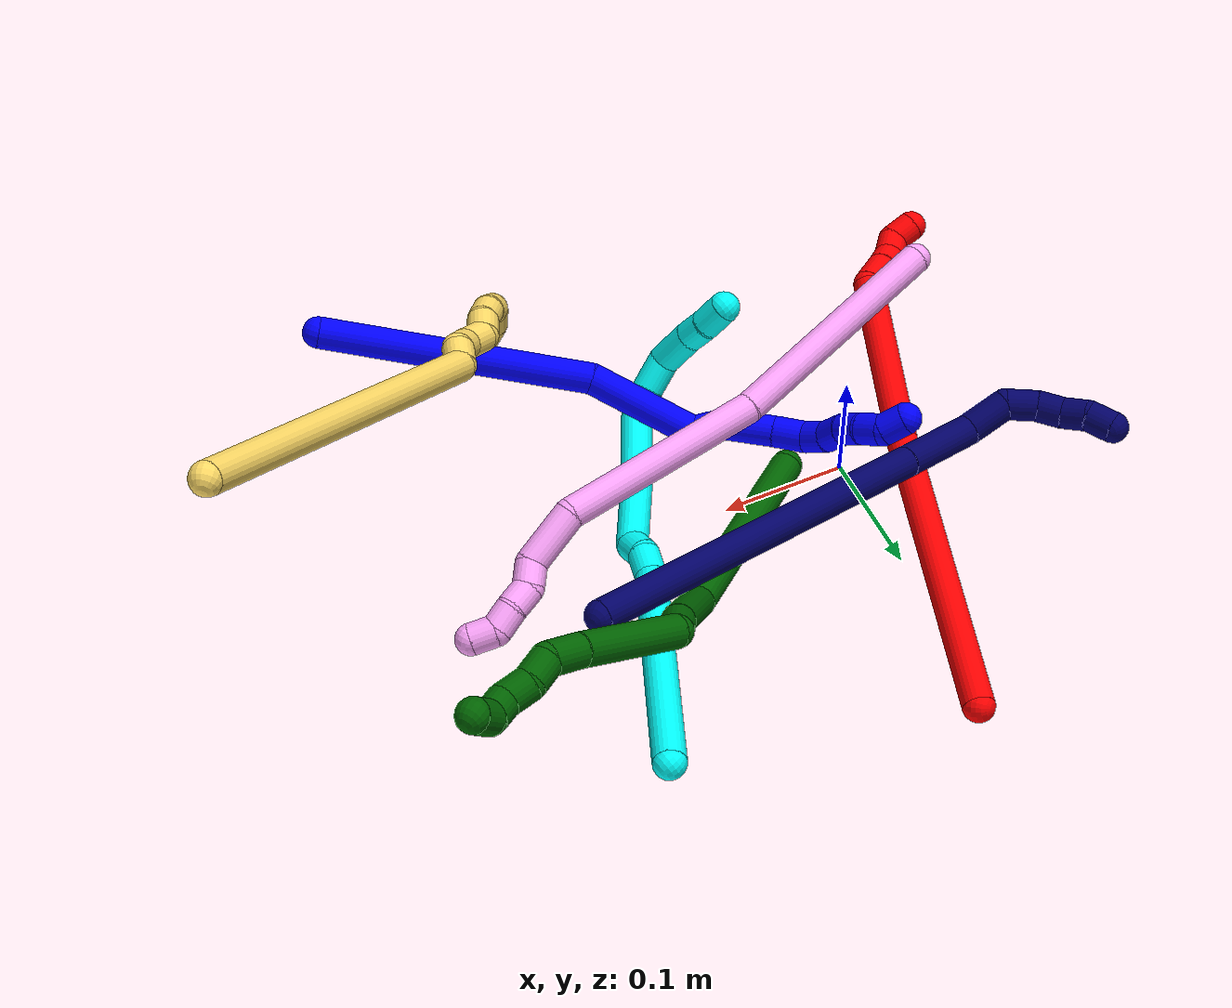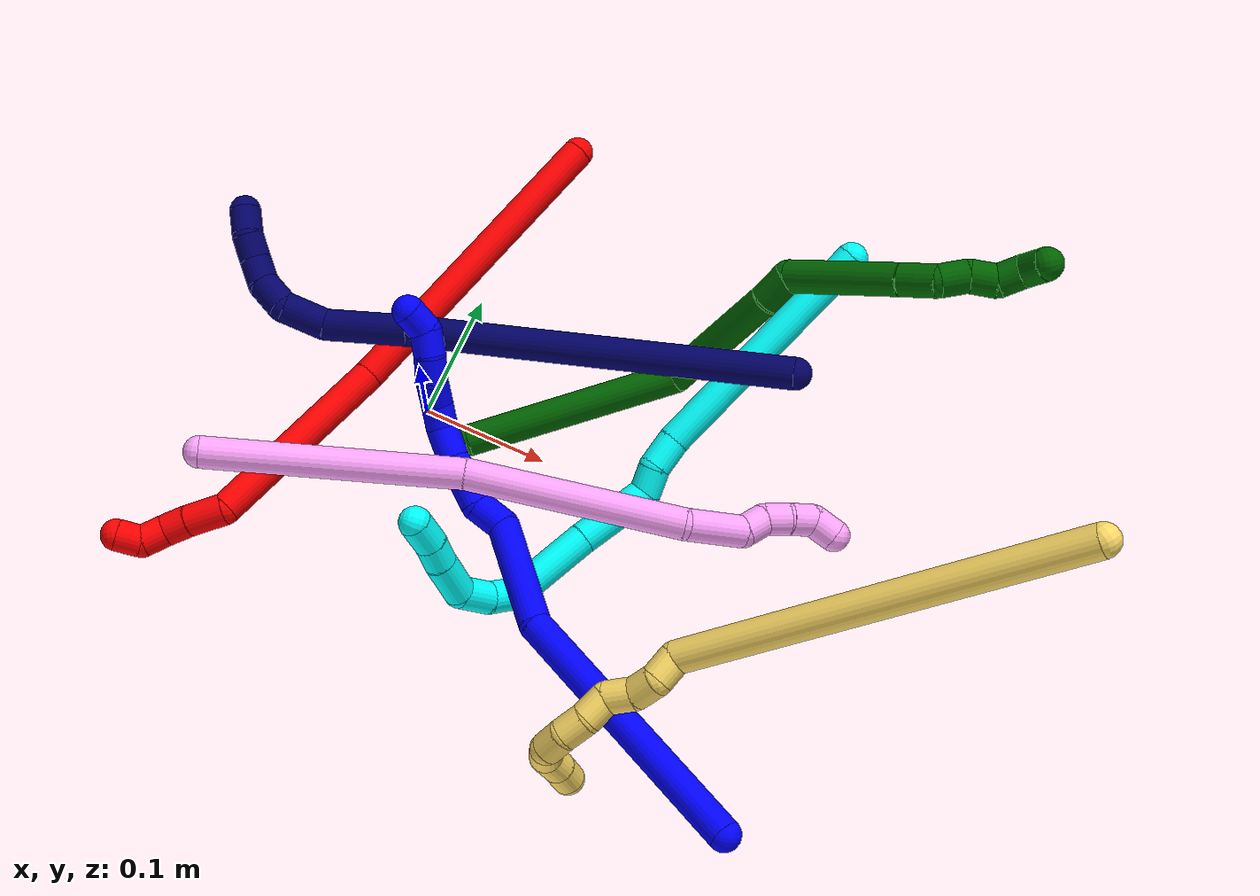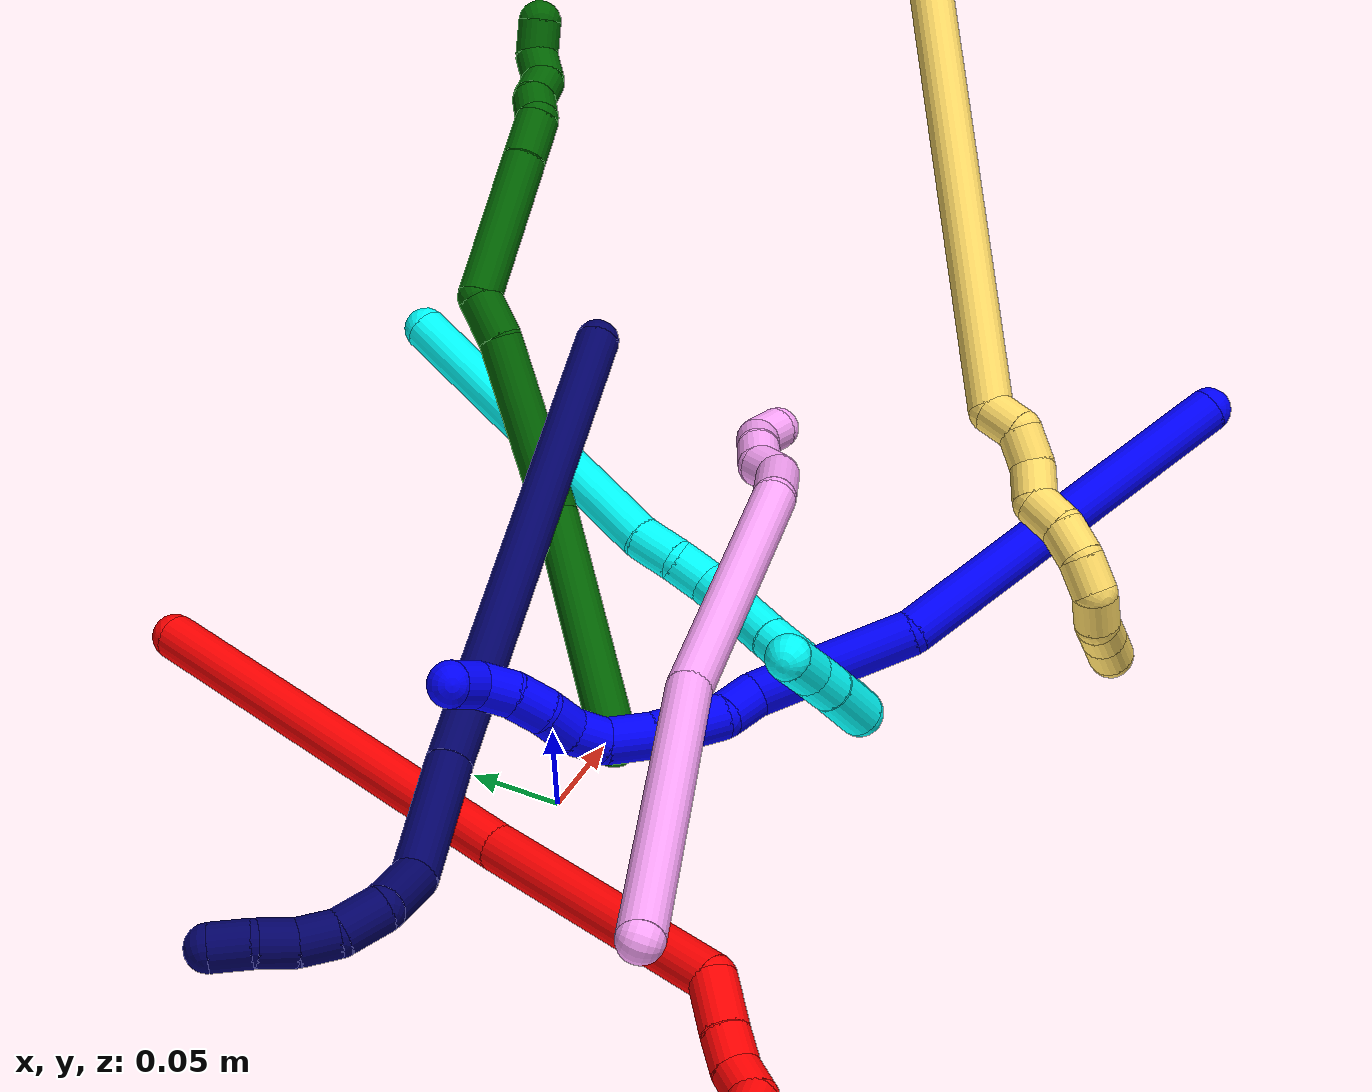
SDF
<sdf version="1.7">
 <world name="default">
  <plugin name="TubeGeneratorPlugin" filename="libtube_generator_plugin.so"/>
  <model name="photoneo_s_sensor">
   <static>1</static>
   <pose>0 0 2 1.57079 1.57079 3.14159</pose>
   <link name="link">
    <inertial><mass>0.1</mass></inertial>
    <sensor name="sensor" type="depth">
     <update_rate>30</update_rate>
     <camera>
      <horizontal_fov>1.22</horizontal_fov>
      <image><width>1920</width><height>1200</height><format>B8G8R8</format></image>
      <clip><near>0.1</near><far>4</far></clip>
      <depth_camera><output>points</output></depth_camera>
     </camera>
     <plugin name="camera_plugin" filename="libgazebo_ros_depth_camera.so">
      <baseline>0.2</baseline>
      <alwaysOn>1</alwaysOn>
      <updateRate>0.0</updateRate>
      <cameraName>camera_ir</cameraName>
      <imageTopicName>/camera/color/image_raw</imageTopicName>
      <cameraInfoTopicName>/camera/color/camera_info</cameraInfoTopicName>
      <depthImageTopicName>/camera/depth/image_raw</depthImageTopicName>
      <depthImageCameraInfoTopicName>/camera/depth/camera_info</depthImageCameraInfoTopicName>
      <pointCloudTopicName>/camera/depth/points</pointCloudTopicName>
      <frameName>fr_optical</frameName>
      <pointCloudCutoff>0.1</pointCloudCutoff>
      <pointCloudCutoffMax>2.0</pointCloudCutoffMax>
      <distortionK1>0</distortionK1>
      <distortionK2>0</distortionK2>
      <distortionK3>0</distortionK3>
      <distortionT1>0</distortionT1>
      <distortionT2>0</distortionT2>
      <CxPrime>0</CxPrime>
      <Cx>0</Cx>
      <Cy>0</Cy>
      <focalLength>0</focalLength>
      <hackBaseline>0</hackBaseline>
     </plugin>
    </sensor>
   </link>
  </model>
  <gravity>0 0 -9.8</gravity>
  <magnetic_field>6e-06 2.3e-05 -4.2e-05</magnetic_field>
  <atmosphere type="adiabatic"/>
  <physics name="default_physics" default="0" type="ode">
   <max_step_size>0.003</max_step_size>
   <real_time_factor>1</real_time_factor>
   <real_time_update_rate>1000</real_time_update_rate>
   <max_contacts>10000</max_contacts>
   <ode>
    <solver>
     <type>quick</type>
     <iters>100</iters>
     <sor>1.3</sor>
     <use_dynamic_moi_rescaling>0</use_dynamic_moi_rescaling>
    </solver>
    <constraints>
     <contact_max_correcting_vel>0</contact_max_correcting_vel>
     <contact_surface_layer>0.001</contact_surface_layer>
     <cfm>0</cfm>
     <erp>0.2</erp>
    </constraints>
   </ode>
  </physics>
  <scene><ambient>0.4 0.4 0.4 1</ambient><background>0.7 0.7 0.7 1</background><shadows>0</shadows></scene>
  <audio><device>default</device></audio>
  <spherical_coordinates>
   <surface_model>EARTH_WGS84</surface_model>
   <latitude_deg>0</latitude_deg>
   <longitude_deg>0</longitude_deg>
   <elevation>0</elevation>
   <heading_deg>0</heading_deg>
  </spherical_coordinates>
  <model name="bin">
   <static>1</static>
   <link name="bottom">
    <collision name="collision-bottom">
     <pose>0 0 -0.01 0 -0 0</pose>
     <geometry><box><size>0.8 0.6 0.02</size></box></geometry>
     <surface>
      <friction><ode><mu>100</mu><mu2>100</mu2></ode></friction>
      <contact><collide_bitmask>65535</collide_bitmask></contact>
     </surface>
    </collision>
   </link>
   <link name="west_wall">
    <collision name="collision-west_wall">
     <pose>-0.41 0 0.1 0 -0 0</pose>
     <geometry><box><size>0.02 0.6 0.2</size></box></geometry>
     <surface>
      <friction><ode><mu>100</mu><mu2>100</mu2></ode></friction>
      <contact><collide_bitmask>65535</collide_bitmask></contact>
     </surface>
    </collision>
   </link>
   <link name="east_wall">
    <collision name="collision-east_wall">
     <pose>0.41 0 0.1 0 -0 0</pose>
     <geometry><box><size>0.02 0.6 0.2</size></box></geometry>
     <surface>
      <friction><ode><mu>100</mu><mu2>100</mu2></ode></friction>
      <contact><collide_bitmask>65535</collide_bitmask></contact>
     </surface>
    </collision>
   </link>
   <link name="south_wall">
    <collision name="collision-south_wall">
     <pose>0 -0.31 0.1 0 -0 0</pose>
     <geometry><box><size>0.8 0.02 0.2</size></box></geometry>
     <surface>
      <friction><ode><mu>100</mu><mu2>100</mu2></ode></friction>
      <contact><collide_bitmask>65535</collide_bitmask></contact>
     </surface>
    </collision>
   </link>
   <link name="north_wall">
    <collision name="collision-north_wall">
     <pose>0 0.31 0.1 0 -0 0</pose>
     <geometry><box><size>0.8 0.02 0.2</size></box></geometry>
     <surface>
      <friction><ode><mu>100</mu><mu2>100</mu2></ode></friction>
      <contact><collide_bitmask>65535</collide_bitmask></contact>
     </surface>
    </collision>
   </link>
  </model>
  <model name="1">
   <static>0</static>
   <link name="1">
    <collision name="collision-cylinder-e_1_1_4">
     <pose>0.028007 0.102945 -0.020155 -1.76414 0.260901 -0.316087</pose>
     <geometry><cylinder><radius>0.0125</radius><length>0.217148</length></cylinder></geometry>
     <surface>
      <friction><ode><mu>1.16</mu><mu2>1.16</mu2><slip1>0</slip1><slip2>0</slip2></ode></friction>
      <contact><ode><kp>1e+06</kp><kd>1</kd><max_vel>0</max_vel><min_depth>0.001</min_depth></ode></contact>
     </surface>
    </collision>
    <visual name="visual-cylinder-e_1_1_4">
     <pose>0.028007 0.102945 -0.020155 -1.76414 0.260901 -0.316087</pose>
     <geometry><cylinder><radius>0.0125</radius><length>0.217148</length></cylinder></geometry>
     <material><ambient>0 0 1 1</ambient></material>
    </visual>
    <collision name="collision-cylinder-e_2_4_5">
     <pose>0.057969 0.25062 -0.03468 -1.44558 0.043336 -0.038225</pose>
     <geometry><cylinder><radius>0.0125</radius><length>0.09025</length></cylinder></geometry>
     <surface>
      <friction><ode><mu>1.16</mu><mu2>1.16</mu2><slip1>0</slip1><slip2>0</slip2></ode></friction>
      <contact><ode><kp>1e+06</kp><kd>1</kd><max_vel>0</max_vel><min_depth>0.001</min_depth></ode></contact>
     </surface>
    </collision>
    <visual name="visual-cylinder-e_2_4_5">
     <pose>0.057969 0.25062 -0.03468 -1.44558 0.043336 -0.038225</pose>
     <geometry><cylinder><radius>0.0125</radius><length>0.09025</length></cylinder></geometry>
     <material><ambient>0 0 1 1</ambient></material>
    </visual>
    <collision name="collision-cylinder-e_3_5_6">
     <pose>0.061685 0.305932 -0.036057 -2.15561 0.137947 -0.255774</pose>
     <geometry><cylinder><radius>0.0125</radius><length>0.025627</length></cylinder></geometry>
     <surface>
      <friction><ode><mu>1.16</mu><mu2>1.16</mu2><slip1>0</slip1><slip2>0</slip2></ode></friction>
      <contact><ode><kp>1e+06</kp><kd>1</kd><max_vel>0</max_vel><min_depth>0.001</min_depth></ode></contact>
     </surface>
    </collision>
    <visual name="visual-cylinder-e_3_5_6">
     <pose>0.061685 0.305932 -0.036057 -2.15561 0.137947 -0.255774</pose>
     <geometry><cylinder><radius>0.0125</radius><length>0.025627</length></cylinder></geometry>
     <material><ambient>0 0 1 1</ambient></material>
    </visual>
    <collision name="collision-cylinder-e_4_6_7">
     <pose>0.061431 0.336282 -0.047275 -1.78073 -0.099442 0.12281</pose>
     <geometry><cylinder><radius>0.0125</radius><length>0.040622</length></cylinder></geometry>
     <surface>
      <friction><ode><mu>1.16</mu><mu2>1.16</mu2><slip1>0</slip1><slip2>0</slip2></ode></friction>
      <contact><ode><kp>1e+06</kp><kd>1</kd><max_vel>0</max_vel><min_depth>0.001</min_depth></ode></contact>
     </surface>
    </collision>
    <visual name="visual-cylinder-e_4_6_7">
     <pose>0.061431 0.336282 -0.047275 -1.78073 -0.099442 0.12281</pose>
     <geometry><cylinder><radius>0.0125</radius><length>0.040622</length></cylinder></geometry>
     <material><ambient>0 0 1 1</ambient></material>
    </visual>
    <collision name="collision-cylinder-e_5_7_8">
     <pose>0.056379 0.36856 -0.053654 -1.74236 -0.234674 0.278308</pose>
     <geometry><cylinder><radius>0.0125</radius><length>0.026111</length></cylinder></geometry>
     <surface>
      <friction><ode><mu>1.16</mu><mu2>1.16</mu2><slip1>0</slip1><slip2>0</slip2></ode></friction>
      <contact><ode><kp>1e+06</kp><kd>1</kd><max_vel>0</max_vel><min_depth>0.001</min_depth></ode></contact>
     </surface>
    </collision>
    <visual name="visual-cylinder-e_5_7_8">
     <pose>0.056379 0.36856 -0.053654 -1.74236 -0.234674 0.278308</pose>
     <geometry><cylinder><radius>0.0125</radius><length>0.026111</length></cylinder></geometry>
     <material><ambient>0 0 1 1</ambient></material>
    </visual>
    <collision name="collision-cylinder-e_6_8_9">
     <pose>0.047414 0.388661 -0.058841 -1.94941 -0.627873 0.892729</pose>
     <geometry><cylinder><radius>0.0125</radius><length>0.020186</length></cylinder></geometry>
     <surface>
      <friction><ode><mu>1.16</mu><mu2>1.16</mu2><slip1>0</slip1><slip2>0</slip2></ode></friction>
      <contact><ode><kp>1e+06</kp><kd>1</kd><max_vel>0</max_vel><min_depth>0.001</min_depth></ode></contact>
     </surface>
    </collision>
    <visual name="visual-cylinder-e_6_8_9">
     <pose>0.047414 0.388661 -0.058841 -1.94941 -0.627873 0.892729</pose>
     <geometry><cylinder><radius>0.0125</radius><length>0.020186</length></cylinder></geometry>
     <material><ambient>0 0 1 1</ambient></material>
    </visual>
    <collision name="collision-cylinder-e_7_9_10">
     <pose>0.03422 0.401347 -0.066477 -2.30686 -0.812843 1.54097</pose>
     <geometry><cylinder><radius>0.0125</radius><length>0.020007</length></cylinder></geometry>
     <surface>
      <friction><ode><mu>1.16</mu><mu2>1.16</mu2><slip1>0</slip1><slip2>0</slip2></ode></friction>
      <contact><ode><kp>1e+06</kp><kd>1</kd><max_vel>0</max_vel><min_depth>0.001</min_depth></ode></contact>
     </surface>
    </collision>
    <visual name="visual-cylinder-e_7_9_10">
     <pose>0.03422 0.401347 -0.066477 -2.30686 -0.812843 1.54097</pose>
     <geometry><cylinder><radius>0.0125</radius><length>0.020007</length></cylinder></geometry>
     <material><ambient>0 0 1 1</ambient></material>
    </visual>
    <collision name="collision-cylinder-e_8_10_11">
     <pose>0.019768 0.412901 -0.073688 -1.95268 -0.801534 1.1197</pose>
     <geometry><cylinder><radius>0.0125</radius><length>0.020007</length></cylinder></geometry>
     <surface>
      <friction><ode><mu>1.16</mu><mu2>1.16</mu2><slip1>0</slip1><slip2>0</slip2></ode></friction>
      <contact><ode><kp>1e+06</kp><kd>1</kd><max_vel>0</max_vel><min_depth>0.001</min_depth></ode></contact>
     </surface>
    </collision>
    <visual name="visual-cylinder-e_8_10_11">
     <pose>0.019768 0.412901 -0.073688 -1.95268 -0.801534 1.1197</pose>
     <geometry><cylinder><radius>0.0125</radius><length>0.020007</length></cylinder></geometry>
     <material><ambient>0 0 1 1</ambient></material>
    </visual>
    <collision name="collision-cylinder-e_9_11_12">
     <pose>0.006914 0.427291 -0.078517 -1.84558 -0.602349 0.778711</pose>
     <geometry><cylinder><radius>0.0125</radius><length>0.020005</length></cylinder></geometry>
     <surface>
      <friction><ode><mu>1.16</mu><mu2>1.16</mu2><slip1>0</slip1><slip2>0</slip2></ode></friction>
      <contact><ode><kp>1e+06</kp><kd>1</kd><max_vel>0</max_vel><min_depth>0.001</min_depth></ode></contact>
     </surface>
    </collision>
    <visual name="visual-cylinder-e_9_11_12">
     <pose>0.006914 0.427291 -0.078517 -1.84558 -0.602349 0.778711</pose>
     <geometry><cylinder><radius>0.0125</radius><length>0.020005</length></cylinder></geometry>
     <material><ambient>0 0 1 1</ambient></material>
    </visual>
    <collision name="collision-cylinder-e_10_12_2">
     <pose>-0.001556 0.441785 -0.087786 -2.3909 -0.283624 0.695241</pose>
     <geometry><cylinder><radius>0.0125</radius><length>0.020036</length></cylinder></geometry>
     <surface>
      <friction><ode><mu>1.16</mu><mu2>1.16</mu2><slip1>0</slip1><slip2>0</slip2></ode></friction>
      <contact><ode><kp>1e+06</kp><kd>1</kd><max_vel>0</max_vel><min_depth>0.001</min_depth></ode></contact>
     </surface>
    </collision>
    <visual name="visual-cylinder-e_10_12_2">
     <pose>-0.001556 0.441785 -0.087786 -2.3909 -0.283624 0.695241</pose>
     <geometry><cylinder><radius>0.0125</radius><length>0.020036</length></cylinder></geometry>
     <material><ambient>0 0 1 1</ambient></material>
    </visual>
    <collision name="collision-sphere-2">
     <pose>-0.00436 0.448346 -0.094819 0 -0 0</pose>
     <geometry><sphere><radius>0.0125</radius></sphere></geometry>
     <surface>
      <friction><ode><mu>1.16</mu><mu2>1.16</mu2><slip1>0</slip1><slip2>0</slip2></ode></friction>
      <contact><ode><kp>1e+06</kp><kd>1</kd><max_vel>0</max_vel><min_depth>0.001</min_depth></ode></contact>
     </surface>
    </collision>
    <visual name="visual-sphere-2">
     <pose>-0.00436 0.448346 -0.094819 0 -0 0</pose>
     <geometry><sphere><radius>0.0125</radius></sphere></geometry>
     <material><ambient>0 0 1 1</ambient></material>
    </visual>
    <collision name="collision-sphere-12">
     <pose>0.001247 0.435224 -0.080754 0 -0 0</pose>
     <geometry><sphere><radius>0.0125</radius></sphere></geometry>
     <surface>
      <friction><ode><mu>1.16</mu><mu2>1.16</mu2><slip1>0</slip1><slip2>0</slip2></ode></friction>
      <contact><ode><kp>1e+06</kp><kd>1</kd><max_vel>0</max_vel><min_depth>0.001</min_depth></ode></contact>
     </surface>
    </collision>
    <visual name="visual-sphere-12">
     <pose>0.001247 0.435224 -0.080754 0 -0 0</pose>
     <geometry><sphere><radius>0.0125</radius></sphere></geometry>
     <material><ambient>0 0 1 1</ambient></material>
    </visual>
    <collision name="collision-sphere-11">
     <pose>0.012581 0.419358 -0.076281 0 -0 0</pose>
     <geometry><sphere><radius>0.0125</radius></sphere></geometry>
     <surface>
      <friction><ode><mu>1.16</mu><mu2>1.16</mu2><slip1>0</slip1><slip2>0</slip2></ode></friction>
      <contact><ode><kp>1e+06</kp><kd>1</kd><max_vel>0</max_vel><min_depth>0.001</min_depth></ode></contact>
     </surface>
    </collision>
    <visual name="visual-sphere-11">
     <pose>0.012581 0.419358 -0.076281 0 -0 0</pose>
     <geometry><sphere><radius>0.0125</radius></sphere></geometry>
     <material><ambient>0 0 1 1</ambient></material>
    </visual>
    <collision name="collision-sphere-10">
     <pose>0.026955 0.406444 -0.071094 0 -0 0</pose>
     <geometry><sphere><radius>0.0125</radius></sphere></geometry>
     <surface>
      <friction><ode><mu>1.16</mu><mu2>1.16</mu2><slip1>0</slip1><slip2>0</slip2></ode></friction>
      <contact><ode><kp>1e+06</kp><kd>1</kd><max_vel>0</max_vel><min_depth>0.001</min_depth></ode></contact>
     </surface>
    </collision>
    <visual name="visual-sphere-10">
     <pose>0.026955 0.406444 -0.071094 0 -0 0</pose>
     <geometry><sphere><radius>0.0125</radius></sphere></geometry>
     <material><ambient>0 0 1 1</ambient></material>
    </visual>
    <collision name="collision-sphere-9">
     <pose>0.041485 0.396251 -0.061861 0 -0 0</pose>
     <geometry><sphere><radius>0.0125</radius></sphere></geometry>
     <surface>
      <friction><ode><mu>1.16</mu><mu2>1.16</mu2><slip1>0</slip1><slip2>0</slip2></ode></friction>
      <contact><ode><kp>1e+06</kp><kd>1</kd><max_vel>0</max_vel><min_depth>0.001</min_depth></ode></contact>
     </surface>
    </collision>
    <visual name="visual-sphere-9">
     <pose>0.041485 0.396251 -0.061861 0 -0 0</pose>
     <geometry><sphere><radius>0.0125</radius></sphere></geometry>
     <material><ambient>0 0 1 1</ambient></material>
    </visual>
    <collision name="collision-sphere-4">
     <pose>0.056014 0.205891 -0.040311 0 -0 0</pose>
     <geometry><sphere><radius>0.0125</radius></sphere></geometry>
     <surface>
      <friction><ode><mu>1.16</mu><mu2>1.16</mu2><slip1>0</slip1><slip2>0</slip2></ode></friction>
      <contact><ode><kp>1e+06</kp><kd>1</kd><max_vel>0</max_vel><min_depth>0.001</min_depth></ode></contact>
     </surface>
    </collision>
    <visual name="visual-sphere-4">
     <pose>0.056014 0.205891 -0.040311 0 -0 0</pose>
     <geometry><sphere><radius>0.0125</radius></sphere></geometry>
     <material><ambient>0 0 1 1</ambient></material>
    </visual>
    <collision name="collision-sphere-1">
     <geometry><sphere><radius>0.0125</radius></sphere></geometry>
     <surface>
      <friction><ode><mu>1.16</mu><mu2>1.16</mu2><slip1>0</slip1><slip2>0</slip2></ode></friction>
      <contact><ode><kp>1e+06</kp><kd>1</kd><max_vel>0</max_vel><min_depth>0.001</min_depth></ode></contact>
     </surface>
    </collision>
    <visual name="visual-sphere-1">
     <geometry><sphere><radius>0.0125</radius></sphere></geometry>
     <material><ambient>0 0 1 1</ambient></material>
    </visual>
    <collision name="collision-sphere-8">
     <pose>0.053343 0.381071 -0.055822 0 -0 0</pose>
     <geometry><sphere><radius>0.0125</radius></sphere></geometry>
     <surface>
      <friction><ode><mu>1.16</mu><mu2>1.16</mu2><slip1>0</slip1><slip2>0</slip2></ode></friction>
      <contact><ode><kp>1e+06</kp><kd>1</kd><max_vel>0</max_vel><min_depth>0.001</min_depth></ode></contact>
     </surface>
    </collision>
    <visual name="visual-sphere-8">
     <pose>0.053343 0.381071 -0.055822 0 -0 0</pose>
     <geometry><sphere><radius>0.0125</radius></sphere></geometry>
     <material><ambient>0 0 1 1</ambient></material>
    </visual>
    <collision name="collision-sphere-5">
     <pose>0.059924 0.29535 -0.02905 0 -0 0</pose>
     <geometry><sphere><radius>0.0125</radius></sphere></geometry>
     <surface>
      <friction><ode><mu>1.16</mu><mu2>1.16</mu2><slip1>0</slip1><slip2>0</slip2></ode></friction>
      <contact><ode><kp>1e+06</kp><kd>1</kd><max_vel>0</max_vel><min_depth>0.001</min_depth></ode></contact>
     </surface>
    </collision>
    <visual name="visual-sphere-5">
     <pose>0.059924 0.29535 -0.02905 0 -0 0</pose>
     <geometry><sphere><radius>0.0125</radius></sphere></geometry>
     <material><ambient>0 0 1 1</ambient></material>
    </visual>
    <collision name="collision-sphere-6">
     <pose>0.063447 0.316515 -0.043063 0 -0 0</pose>
     <geometry><sphere><radius>0.0125</radius></sphere></geometry>
     <surface>
      <friction><ode><mu>1.16</mu><mu2>1.16</mu2><slip1>0</slip1><slip2>0</slip2></ode></friction>
      <contact><ode><kp>1e+06</kp><kd>1</kd><max_vel>0</max_vel><min_depth>0.001</min_depth></ode></contact>
     </surface>
    </collision>
    <visual name="visual-sphere-6">
     <pose>0.063447 0.316515 -0.043063 0 -0 0</pose>
     <geometry><sphere><radius>0.0125</radius></sphere></geometry>
     <material><ambient>0 0 1 1</ambient></material>
    </visual>
    <collision name="collision-sphere-7">
     <pose>0.059415 0.356049 -0.051486 0 -0 0</pose>
     <geometry><sphere><radius>0.0125</radius></sphere></geometry>
     <surface>
      <friction><ode><mu>1.16</mu><mu2>1.16</mu2><slip1>0</slip1><slip2>0</slip2></ode></friction>
      <contact><ode><kp>1e+06</kp><kd>1</kd><max_vel>0</max_vel><min_depth>0.001</min_depth></ode></contact>
     </surface>
    </collision>
    <visual name="visual-sphere-7">
     <pose>0.059415 0.356049 -0.051486 0 -0 0</pose>
     <geometry><sphere><radius>0.0125</radius></sphere></geometry>
     <material><ambient>0 0 1 1</ambient></material>
    </visual>
    <inertial>
     <pose>0.038012 0.235266 -0.038147 0 -0 0</pose>
     <mass>0.5</mass>
     <inertia>
      <ixx>0.000615</ixx>
      <ixy>0</ixy>
      <ixz>0</ixz>
      <iyy>-0.000304</iyy>
      <iyz>0</iyz>
      <izz>-0.001125</izz>
     </inertia>
    </inertial>
   </link>
   <pose>0.344964 -0.224132 0.098502 -2.89065 0.903148 -2.14565</pose>
  </model>
  <model name="2">
   <static>0</static>
   <link name="2">
    <collision name="collision-cylinder-e_1_1_4">
     <pose>0.020908 -0.103997 0.069126 0.984159 0.165895 0.089076</pose>
     <geometry><cylinder><radius>0.0125</radius><length>0.253227</length></cylinder></geometry>
     <surface>
      <friction><ode><mu>1.16</mu><mu2>1.16</mu2><slip1>0</slip1><slip2>0</slip2></ode></friction>
      <contact><ode><kp>1e+06</kp><kd>1</kd><max_vel>0</max_vel><min_depth>0.001</min_depth></ode></contact>
     </surface>
    </collision>
    <visual name="visual-cylinder-e_1_1_4">
     <pose>0.020908 -0.103997 0.069126 0.984159 0.165895 0.089076</pose>
     <geometry><cylinder><radius>0.0125</radius><length>0.253227</length></cylinder></geometry>
     <material><ambient>1 0 0 1</ambient></material>
    </visual>
    <collision name="collision-cylinder-e_2_4_5">
     <pose>0.050174 -0.275927 0.175564 1.06855 0.10742 0.063597</pose>
     <geometry><cylinder><radius>0.0125</radius><length>0.155909</length></cylinder></geometry>
     <surface>
      <friction><ode><mu>1.16</mu><mu2>1.16</mu2><slip1>0</slip1><slip2>0</slip2></ode></friction>
      <contact><ode><kp>1e+06</kp><kd>1</kd><max_vel>0</max_vel><min_depth>0.001</min_depth></ode></contact>
     </surface>
    </collision>
    <visual name="visual-cylinder-e_2_4_5">
     <pose>0.050174 -0.275927 0.175564 1.06855 0.10742 0.063597</pose>
     <geometry><cylinder><radius>0.0125</radius><length>0.155909</length></cylinder></geometry>
     <material><ambient>1 0 0 1</ambient></material>
    </visual>
    <collision name="collision-cylinder-e_3_5_6">
     <pose>0.068457 -0.355461 0.214697 1.41496 0.70172 0.60666</pose>
     <geometry><cylinder><radius>0.0125</radius><length>0.030749</length></cylinder></geometry>
     <surface>
      <friction><ode><mu>1.16</mu><mu2>1.16</mu2><slip1>0</slip1><slip2>0</slip2></ode></friction>
      <contact><ode><kp>1e+06</kp><kd>1</kd><max_vel>0</max_vel><min_depth>0.001</min_depth></ode></contact>
     </surface>
    </collision>
    <visual name="visual-cylinder-e_3_5_6">
     <pose>0.068457 -0.355461 0.214697 1.41496 0.70172 0.60666</pose>
     <geometry><cylinder><radius>0.0125</radius><length>0.030749</length></cylinder></geometry>
     <material><ambient>1 0 0 1</ambient></material>
    </visual>
    <collision name="collision-cylinder-e_4_6_7">
     <pose>0.085024 -0.374357 0.218427 1.31513 0.722023 0.567383</pose>
     <geometry><cylinder><radius>0.0125</radius><length>0.020099</length></cylinder></geometry>
     <surface>
      <friction><ode><mu>1.16</mu><mu2>1.16</mu2><slip1>0</slip1><slip2>0</slip2></ode></friction>
      <contact><ode><kp>1e+06</kp><kd>1</kd><max_vel>0</max_vel><min_depth>0.001</min_depth></ode></contact>
     </surface>
    </collision>
    <visual name="visual-cylinder-e_4_6_7">
     <pose>0.085024 -0.374357 0.218427 1.31513 0.722023 0.567383</pose>
     <geometry><cylinder><radius>0.0125</radius><length>0.020099</length></cylinder></geometry>
     <material><ambient>1 0 0 1</ambient></material>
    </visual>
    <collision name="collision-cylinder-e_5_7_8">
     <pose>0.095383 -0.390676 0.222545 1.33046 0.380646 0.300011</pose>
     <geometry><cylinder><radius>0.0125</radius><length>0.020011</length></cylinder></geometry>
     <surface>
      <friction><ode><mu>1.16</mu><mu2>1.16</mu2><slip1>0</slip1><slip2>0</slip2></ode></friction>
      <contact><ode><kp>1e+06</kp><kd>1</kd><max_vel>0</max_vel><min_depth>0.001</min_depth></ode></contact>
     </surface>
    </collision>
    <visual name="visual-cylinder-e_5_7_8">
     <pose>0.095383 -0.390676 0.222545 1.33046 0.380646 0.300011</pose>
     <geometry><cylinder><radius>0.0125</radius><length>0.020011</length></cylinder></geometry>
     <material><ambient>1 0 0 1</ambient></material>
    </visual>
    <collision name="collision-cylinder-e_6_8_2">
     <pose>0.103019 -0.407632 0.220093 2.10217 0.402586 0.685141</pose>
     <geometry><cylinder><radius>0.0125</radius><length>0.020005</length></cylinder></geometry>
     <surface>
      <friction><ode><mu>1.16</mu><mu2>1.16</mu2><slip1>0</slip1><slip2>0</slip2></ode></friction>
      <contact><ode><kp>1e+06</kp><kd>1</kd><max_vel>0</max_vel><min_depth>0.001</min_depth></ode></contact>
     </surface>
    </collision>
    <visual name="visual-cylinder-e_6_8_2">
     <pose>0.103019 -0.407632 0.220093 2.10217 0.402586 0.685141</pose>
     <geometry><cylinder><radius>0.0125</radius><length>0.020005</length></cylinder></geometry>
     <material><ambient>1 0 0 1</ambient></material>
    </visual>
    <collision name="collision-sphere-2">
     <pose>0.106938 -0.415566 0.21543 0 -0 0</pose>
     <geometry><sphere><radius>0.0125</radius></sphere></geometry>
     <surface>
      <friction><ode><mu>1.16</mu><mu2>1.16</mu2><slip1>0</slip1><slip2>0</slip2></ode></friction>
      <contact><ode><kp>1e+06</kp><kd>1</kd><max_vel>0</max_vel><min_depth>0.001</min_depth></ode></contact>
     </surface>
    </collision>
    <visual name="visual-sphere-2">
     <pose>0.106938 -0.415566 0.21543 0 -0 0</pose>
     <geometry><sphere><radius>0.0125</radius></sphere></geometry>
     <material><ambient>1 0 0 1</ambient></material>
    </visual>
    <collision name="collision-sphere-4">
     <pose>0.041817 -0.207994 0.138253 0 -0 0</pose>
     <geometry><sphere><radius>0.0125</radius></sphere></geometry>
     <surface>
      <friction><ode><mu>1.16</mu><mu2>1.16</mu2><slip1>0</slip1><slip2>0</slip2></ode></friction>
      <contact><ode><kp>1e+06</kp><kd>1</kd><max_vel>0</max_vel><min_depth>0.001</min_depth></ode></contact>
     </surface>
    </collision>
    <visual name="visual-sphere-4">
     <pose>0.041817 -0.207994 0.138253 0 -0 0</pose>
     <geometry><sphere><radius>0.0125</radius></sphere></geometry>
     <material><ambient>1 0 0 1</ambient></material>
    </visual>
    <collision name="collision-sphere-1">
     <geometry><sphere><radius>0.0125</radius></sphere></geometry>
     <surface>
      <friction><ode><mu>1.16</mu><mu2>1.16</mu2><slip1>0</slip1><slip2>0</slip2></ode></friction>
      <contact><ode><kp>1e+06</kp><kd>1</kd><max_vel>0</max_vel><min_depth>0.001</min_depth></ode></contact>
     </surface>
    </collision>
    <visual name="visual-sphere-1">
     <geometry><sphere><radius>0.0125</radius></sphere></geometry>
     <material><ambient>1 0 0 1</ambient></material>
    </visual>
    <collision name="collision-sphere-8">
     <pose>0.0991 -0.399698 0.224756 0 -0 0</pose>
     <geometry><sphere><radius>0.0125</radius></sphere></geometry>
     <surface>
      <friction><ode><mu>1.16</mu><mu2>1.16</mu2><slip1>0</slip1><slip2>0</slip2></ode></friction>
      <contact><ode><kp>1e+06</kp><kd>1</kd><max_vel>0</max_vel><min_depth>0.001</min_depth></ode></contact>
     </surface>
    </collision>
    <visual name="visual-sphere-8">
     <pose>0.0991 -0.399698 0.224756 0 -0 0</pose>
     <geometry><sphere><radius>0.0125</radius></sphere></geometry>
     <material><ambient>1 0 0 1</ambient></material>
    </visual>
    <collision name="collision-sphere-5">
     <pose>0.058532 -0.343861 0.212874 0 -0 0</pose>
     <geometry><sphere><radius>0.0125</radius></sphere></geometry>
     <surface>
      <friction><ode><mu>1.16</mu><mu2>1.16</mu2><slip1>0</slip1><slip2>0</slip2></ode></friction>
      <contact><ode><kp>1e+06</kp><kd>1</kd><max_vel>0</max_vel><min_depth>0.001</min_depth></ode></contact>
     </surface>
    </collision>
    <visual name="visual-sphere-5">
     <pose>0.058532 -0.343861 0.212874 0 -0 0</pose>
     <geometry><sphere><radius>0.0125</radius></sphere></geometry>
     <material><ambient>1 0 0 1</ambient></material>
    </visual>
    <collision name="collision-sphere-6">
     <pose>0.078382 -0.36706 0.216519 0 -0 0</pose>
     <geometry><sphere><radius>0.0125</radius></sphere></geometry>
     <surface>
      <friction><ode><mu>1.16</mu><mu2>1.16</mu2><slip1>0</slip1><slip2>0</slip2></ode></friction>
      <contact><ode><kp>1e+06</kp><kd>1</kd><max_vel>0</max_vel><min_depth>0.001</min_depth></ode></contact>
     </surface>
    </collision>
    <visual name="visual-sphere-6">
     <pose>0.078382 -0.36706 0.216519 0 -0 0</pose>
     <geometry><sphere><radius>0.0125</radius></sphere></geometry>
     <material><ambient>1 0 0 1</ambient></material>
    </visual>
    <collision name="collision-sphere-7">
     <pose>0.091665 -0.381654 0.220334 0 -0 0</pose>
     <geometry><sphere><radius>0.0125</radius></sphere></geometry>
     <surface>
      <friction><ode><mu>1.16</mu><mu2>1.16</mu2><slip1>0</slip1><slip2>0</slip2></ode></friction>
      <contact><ode><kp>1e+06</kp><kd>1</kd><max_vel>0</max_vel><min_depth>0.001</min_depth></ode></contact>
     </surface>
    </collision>
    <visual name="visual-sphere-7">
     <pose>0.091665 -0.381654 0.220334 0 -0 0</pose>
     <geometry><sphere><radius>0.0125</radius></sphere></geometry>
     <material><ambient>1 0 0 1</ambient></material>
    </visual>
    <inertial>
     <pose>0.041801 -0.207562 0.12945 0 -0 0</pose>
     <mass>0.5</mass>
     <inertia>
      <ixx>0.001816</ixx>
      <ixy>0</ixy>
      <ixz>0</ixz>
      <iyy>0.001038</iyy>
      <iyz>0</iyz>
      <izz>0.001159</izz>
     </inertia>
    </inertial>
   </link>
   <pose>0.016565 0.24785 0.011499 -2.31904 0.949218 -3.1309</pose>
  </model>
  <model name="3">
   <static>0</static>
   <link name="3">
    <collision name="collision-cylinder-e_1_1_4">
     <pose>-0.01605 -0.08732 -0.041835 2.01758 -0.164268 -0.259962</pose>
     <geometry><cylinder><radius>0.0125</radius><length>0.19629</length></cylinder></geometry>
     <surface>
      <friction><ode><mu>1.16</mu><mu2>1.16</mu2><slip1>0</slip1><slip2>0</slip2></ode></friction>
      <contact><ode><kp>1e+06</kp><kd>1</kd><max_vel>0</max_vel><min_depth>0.001</min_depth></ode></contact>
     </surface>
    </collision>
    <visual name="visual-cylinder-e_1_1_4">
     <pose>-0.01605 -0.08732 -0.041835 2.01758 -0.164268 -0.259962</pose>
     <geometry><cylinder><radius>0.0125</radius><length>0.19629</length></cylinder></geometry>
     <material><ambient>0.003922 1 0.996078 1</ambient></material>
    </visual>
    <collision name="collision-cylinder-e_2_4_5">
     <pose>-0.035958 -0.185996 -0.087634 1.90666 -0.310433 -0.433785</pose>
     <geometry><cylinder><radius>0.0125</radius><length>0.025265</length></cylinder></geometry>
     <surface>
      <friction><ode><mu>1.16</mu><mu2>1.16</mu2><slip1>0</slip1><slip2>0</slip2></ode></friction>
      <contact><ode><kp>1e+06</kp><kd>1</kd><max_vel>0</max_vel><min_depth>0.001</min_depth></ode></contact>
     </surface>
    </collision>
    <visual name="visual-cylinder-e_2_4_5">
     <pose>-0.035958 -0.185996 -0.087634 1.90666 -0.310433 -0.433785</pose>
     <geometry><cylinder><radius>0.0125</radius><length>0.025265</length></cylinder></geometry>
     <material><ambient>0.003922 1 0.996078 1</ambient></material>
    </visual>
    <collision name="collision-cylinder-e_3_5_6">
     <pose>-0.040951 -0.208229 -0.091478 1.55972 -0.10383 -0.102688</pose>
     <geometry><cylinder><radius>0.0125</radius><length>0.021872</length></cylinder></geometry>
     <surface>
      <friction><ode><mu>1.16</mu><mu2>1.16</mu2><slip1>0</slip1><slip2>0</slip2></ode></friction>
      <contact><ode><kp>1e+06</kp><kd>1</kd><max_vel>0</max_vel><min_depth>0.001</min_depth></ode></contact>
     </surface>
    </collision>
    <visual name="visual-cylinder-e_3_5_6">
     <pose>-0.040951 -0.208229 -0.091478 1.55972 -0.10383 -0.102688</pose>
     <geometry><cylinder><radius>0.0125</radius><length>0.021872</length></cylinder></geometry>
     <material><ambient>0.003922 1 0.996078 1</ambient></material>
    </visual>
    <collision name="collision-cylinder-e_4_6_7">
     <pose>-0.051197 -0.241451 -0.109701 2.25814 -0.305373 -0.629209</pose>
     <geometry><cylinder><radius>0.0125</radius><length>0.060625</length></cylinder></geometry>
     <surface>
      <friction><ode><mu>1.16</mu><mu2>1.16</mu2><slip1>0</slip1><slip2>0</slip2></ode></friction>
      <contact><ode><kp>1e+06</kp><kd>1</kd><max_vel>0</max_vel><min_depth>0.001</min_depth></ode></contact>
     </surface>
    </collision>
    <visual name="visual-cylinder-e_4_6_7">
     <pose>-0.051197 -0.241451 -0.109701 2.25814 -0.305373 -0.629209</pose>
     <geometry><cylinder><radius>0.0125</radius><length>0.060625</length></cylinder></geometry>
     <material><ambient>0.003922 1 0.996078 1</ambient></material>
    </visual>
    <collision name="collision-cylinder-e_5_7_8">
     <pose>-0.070712 -0.28948 -0.146643 2.19759 -0.316942 -0.606784</pose>
     <geometry><cylinder><radius>0.0125</radius><length>0.066746</length></cylinder></geometry>
     <surface>
      <friction><ode><mu>1.16</mu><mu2>1.16</mu2><slip1>0</slip1><slip2>0</slip2></ode></friction>
      <contact><ode><kp>1e+06</kp><kd>1</kd><max_vel>0</max_vel><min_depth>0.001</min_depth></ode></contact>
     </surface>
    </collision>
    <visual name="visual-cylinder-e_5_7_8">
     <pose>-0.070712 -0.28948 -0.146643 2.19759 -0.316942 -0.606784</pose>
     <geometry><cylinder><radius>0.0125</radius><length>0.066746</length></cylinder></geometry>
     <material><ambient>0.003922 1 0.996078 1</ambient></material>
    </visual>
    <collision name="collision-cylinder-e_6_8_9">
     <pose>-0.085943 -0.318371 -0.175454 2.83713 -0.423909 -1.90285</pose>
     <geometry><cylinder><radius>0.0125</radius><length>0.023484</length></cylinder></geometry>
     <surface>
      <friction><ode><mu>1.16</mu><mu2>1.16</mu2><slip1>0</slip1><slip2>0</slip2></ode></friction>
      <contact><ode><kp>1e+06</kp><kd>1</kd><max_vel>0</max_vel><min_depth>0.001</min_depth></ode></contact>
     </surface>
    </collision>
    <visual name="visual-cylinder-e_6_8_9">
     <pose>-0.085943 -0.318371 -0.175454 2.83713 -0.423909 -1.90285</pose>
     <geometry><cylinder><radius>0.0125</radius><length>0.023484</length></cylinder></geometry>
     <material><ambient>0.003922 1 0.996078 1</ambient></material>
    </visual>
    <collision name="collision-cylinder-e_7_9_10">
     <pose>-0.096645 -0.320575 -0.198031 -3.06056 -0.442086 2.78464</pose>
     <geometry><cylinder><radius>0.0125</radius><length>0.027454</length></cylinder></geometry>
     <surface>
      <friction><ode><mu>1.16</mu><mu2>1.16</mu2><slip1>0</slip1><slip2>0</slip2></ode></friction>
      <contact><ode><kp>1e+06</kp><kd>1</kd><max_vel>0</max_vel><min_depth>0.001</min_depth></ode></contact>
     </surface>
    </collision>
    <visual name="visual-cylinder-e_7_9_10">
     <pose>-0.096645 -0.320575 -0.198031 -3.06056 -0.442086 2.78464</pose>
     <geometry><cylinder><radius>0.0125</radius><length>0.027454</length></cylinder></geometry>
     <material><ambient>0.003922 1 0.996078 1</ambient></material>
    </visual>
    <collision name="collision-cylinder-e_8_10_11">
     <pose>-0.108223 -0.308525 -0.222511 -2.40229 -0.334872 0.822666</pose>
     <geometry><cylinder><radius>0.0125</radius><length>0.034716</length></cylinder></geometry>
     <surface>
      <friction><ode><mu>1.16</mu><mu2>1.16</mu2><slip1>0</slip1><slip2>0</slip2></ode></friction>
      <contact><ode><kp>1e+06</kp><kd>1</kd><max_vel>0</max_vel><min_depth>0.001</min_depth></ode></contact>
     </surface>
    </collision>
    <visual name="visual-cylinder-e_8_10_11">
     <pose>-0.108223 -0.308525 -0.222511 -2.40229 -0.334872 0.822666</pose>
     <geometry><cylinder><radius>0.0125</radius><length>0.034716</length></cylinder></geometry>
     <material><ambient>0.003922 1 0.996078 1</ambient></material>
    </visual>
    <collision name="collision-cylinder-e_9_11_12">
     <pose>-0.116617 -0.290394 -0.241169 -2.31648 -0.271979 0.606027</pose>
     <geometry><cylinder><radius>0.0125</radius><length>0.020025</length></cylinder></geometry>
     <surface>
      <friction><ode><mu>1.16</mu><mu2>1.16</mu2><slip1>0</slip1><slip2>0</slip2></ode></friction>
      <contact><ode><kp>1e+06</kp><kd>1</kd><max_vel>0</max_vel><min_depth>0.001</min_depth></ode></contact>
     </surface>
    </collision>
    <visual name="visual-cylinder-e_9_11_12">
     <pose>-0.116617 -0.290394 -0.241169 -2.31648 -0.271979 0.606027</pose>
     <geometry><cylinder><radius>0.0125</radius><length>0.020025</length></cylinder></geometry>
     <material><ambient>0.003922 1 0.996078 1</ambient></material>
    </visual>
    <collision name="collision-cylinder-e_10_12_2">
     <pose>-0.122922 -0.276276 -0.256419 -2.46213 -0.31241 0.83837</pose>
     <geometry><cylinder><radius>0.0125</radius><length>0.023523</length></cylinder></geometry>
     <surface>
      <friction><ode><mu>1.16</mu><mu2>1.16</mu2><slip1>0</slip1><slip2>0</slip2></ode></friction>
      <contact><ode><kp>1e+06</kp><kd>1</kd><max_vel>0</max_vel><min_depth>0.001</min_depth></ode></contact>
     </surface>
    </collision>
    <visual name="visual-cylinder-e_10_12_2">
     <pose>-0.122922 -0.276276 -0.256419 -2.46213 -0.31241 0.83837</pose>
     <geometry><cylinder><radius>0.0125</radius><length>0.023523</length></cylinder></geometry>
     <material><ambient>0.003922 1 0.996078 1</ambient></material>
    </visual>
    <collision name="collision-sphere-2">
     <pose>-0.126537 -0.269243 -0.265126 0 -0 0</pose>
     <geometry><sphere><radius>0.0125</radius></sphere></geometry>
     <surface>
      <friction><ode><mu>1.16</mu><mu2>1.16</mu2><slip1>0</slip1><slip2>0</slip2></ode></friction>
      <contact><ode><kp>1e+06</kp><kd>1</kd><max_vel>0</max_vel><min_depth>0.001</min_depth></ode></contact>
     </surface>
    </collision>
    <visual name="visual-sphere-2">
     <pose>-0.126537 -0.269243 -0.265126 0 -0 0</pose>
     <geometry><sphere><radius>0.0125</radius></sphere></geometry>
     <material><ambient>0.003922 1 0.996078 1</ambient></material>
    </visual>
    <collision name="collision-sphere-12">
     <pose>-0.119307 -0.283309 -0.247712 0 -0 0</pose>
     <geometry><sphere><radius>0.0125</radius></sphere></geometry>
     <surface>
      <friction><ode><mu>1.16</mu><mu2>1.16</mu2><slip1>0</slip1><slip2>0</slip2></ode></friction>
      <contact><ode><kp>1e+06</kp><kd>1</kd><max_vel>0</max_vel><min_depth>0.001</min_depth></ode></contact>
     </surface>
    </collision>
    <visual name="visual-sphere-12">
     <pose>-0.119307 -0.283309 -0.247712 0 -0 0</pose>
     <geometry><sphere><radius>0.0125</radius></sphere></geometry>
     <material><ambient>0.003922 1 0.996078 1</ambient></material>
    </visual>
    <collision name="collision-sphere-11">
     <pose>-0.113927 -0.297479 -0.234625 0 -0 0</pose>
     <geometry><sphere><radius>0.0125</radius></sphere></geometry>
     <surface>
      <friction><ode><mu>1.16</mu><mu2>1.16</mu2><slip1>0</slip1><slip2>0</slip2></ode></friction>
      <contact><ode><kp>1e+06</kp><kd>1</kd><max_vel>0</max_vel><min_depth>0.001</min_depth></ode></contact>
     </surface>
    </collision>
    <visual name="visual-sphere-11">
     <pose>-0.113927 -0.297479 -0.234625 0 -0 0</pose>
     <geometry><sphere><radius>0.0125</radius></sphere></geometry>
     <material><ambient>0.003922 1 0.996078 1</ambient></material>
    </visual>
    <collision name="collision-sphere-10">
     <pose>-0.102518 -0.319571 -0.210397 0 -0 0</pose>
     <geometry><sphere><radius>0.0125</radius></sphere></geometry>
     <surface>
      <friction><ode><mu>1.16</mu><mu2>1.16</mu2><slip1>0</slip1><slip2>0</slip2></ode></friction>
      <contact><ode><kp>1e+06</kp><kd>1</kd><max_vel>0</max_vel><min_depth>0.001</min_depth></ode></contact>
     </surface>
    </collision>
    <visual name="visual-sphere-10">
     <pose>-0.102518 -0.319571 -0.210397 0 -0 0</pose>
     <geometry><sphere><radius>0.0125</radius></sphere></geometry>
     <material><ambient>0.003922 1 0.996078 1</ambient></material>
    </visual>
    <collision name="collision-sphere-9">
     <pose>-0.090773 -0.321579 -0.185664 0 -0 0</pose>
     <geometry><sphere><radius>0.0125</radius></sphere></geometry>
     <surface>
      <friction><ode><mu>1.16</mu><mu2>1.16</mu2><slip1>0</slip1><slip2>0</slip2></ode></friction>
      <contact><ode><kp>1e+06</kp><kd>1</kd><max_vel>0</max_vel><min_depth>0.001</min_depth></ode></contact>
     </surface>
    </collision>
    <visual name="visual-sphere-9">
     <pose>-0.090773 -0.321579 -0.185664 0 -0 0</pose>
     <geometry><sphere><radius>0.0125</radius></sphere></geometry>
     <material><ambient>0.003922 1 0.996078 1</ambient></material>
    </visual>
    <collision name="collision-sphere-4">
     <pose>-0.032099 -0.17464 -0.08367 0 -0 0</pose>
     <geometry><sphere><radius>0.0125</radius></sphere></geometry>
     <surface>
      <friction><ode><mu>1.16</mu><mu2>1.16</mu2><slip1>0</slip1><slip2>0</slip2></ode></friction>
      <contact><ode><kp>1e+06</kp><kd>1</kd><max_vel>0</max_vel><min_depth>0.001</min_depth></ode></contact>
     </surface>
    </collision>
    <visual name="visual-sphere-4">
     <pose>-0.032099 -0.17464 -0.08367 0 -0 0</pose>
     <geometry><sphere><radius>0.0125</radius></sphere></geometry>
     <material><ambient>0.003922 1 0.996078 1</ambient></material>
    </visual>
    <collision name="collision-sphere-1">
     <geometry><sphere><radius>0.0125</radius></sphere></geometry>
     <surface>
      <friction><ode><mu>1.16</mu><mu2>1.16</mu2><slip1>0</slip1><slip2>0</slip2></ode></friction>
      <contact><ode><kp>1e+06</kp><kd>1</kd><max_vel>0</max_vel><min_depth>0.001</min_depth></ode></contact>
     </surface>
    </collision>
    <visual name="visual-sphere-1">
     <geometry><sphere><radius>0.0125</radius></sphere></geometry>
     <material><ambient>0.003922 1 0.996078 1</ambient></material>
    </visual>
    <collision name="collision-sphere-8">
     <pose>-0.081113 -0.315162 -0.165243 0 -0 0</pose>
     <geometry><sphere><radius>0.0125</radius></sphere></geometry>
     <surface>
      <friction><ode><mu>1.16</mu><mu2>1.16</mu2><slip1>0</slip1><slip2>0</slip2></ode></friction>
      <contact><ode><kp>1e+06</kp><kd>1</kd><max_vel>0</max_vel><min_depth>0.001</min_depth></ode></contact>
     </surface>
    </collision>
    <visual name="visual-sphere-8">
     <pose>-0.081113 -0.315162 -0.165243 0 -0 0</pose>
     <geometry><sphere><radius>0.0125</radius></sphere></geometry>
     <material><ambient>0.003922 1 0.996078 1</ambient></material>
    </visual>
    <collision name="collision-sphere-5">
     <pose>-0.039817 -0.197353 -0.091598 0 -0 0</pose>
     <geometry><sphere><radius>0.0125</radius></sphere></geometry>
     <surface>
      <friction><ode><mu>1.16</mu><mu2>1.16</mu2><slip1>0</slip1><slip2>0</slip2></ode></friction>
      <contact><ode><kp>1e+06</kp><kd>1</kd><max_vel>0</max_vel><min_depth>0.001</min_depth></ode></contact>
     </surface>
    </collision>
    <visual name="visual-sphere-5">
     <pose>-0.039817 -0.197353 -0.091598 0 -0 0</pose>
     <geometry><sphere><radius>0.0125</radius></sphere></geometry>
     <material><ambient>0.003922 1 0.996078 1</ambient></material>
    </visual>
    <collision name="collision-sphere-6">
     <pose>-0.042084 -0.219106 -0.091358 0 -0 0</pose>
     <geometry><sphere><radius>0.0125</radius></sphere></geometry>
     <surface>
      <friction><ode><mu>1.16</mu><mu2>1.16</mu2><slip1>0</slip1><slip2>0</slip2></ode></friction>
      <contact><ode><kp>1e+06</kp><kd>1</kd><max_vel>0</max_vel><min_depth>0.001</min_depth></ode></contact>
     </surface>
    </collision>
    <visual name="visual-sphere-6">
     <pose>-0.042084 -0.219106 -0.091358 0 -0 0</pose>
     <geometry><sphere><radius>0.0125</radius></sphere></geometry>
     <material><ambient>0.003922 1 0.996078 1</ambient></material>
    </visual>
    <collision name="collision-sphere-7">
     <pose>-0.060311 -0.263797 -0.128044 0 -0 0</pose>
     <geometry><sphere><radius>0.0125</radius></sphere></geometry>
     <surface>
      <friction><ode><mu>1.16</mu><mu2>1.16</mu2><slip1>0</slip1><slip2>0</slip2></ode></friction>
      <contact><ode><kp>1e+06</kp><kd>1</kd><max_vel>0</max_vel><min_depth>0.001</min_depth></ode></contact>
     </surface>
    </collision>
    <visual name="visual-sphere-7">
     <pose>-0.060311 -0.263797 -0.128044 0 -0 0</pose>
     <geometry><sphere><radius>0.0125</radius></sphere></geometry>
     <material><ambient>0.003922 1 0.996078 1</ambient></material>
    </visual>
    <inertial>
     <pose>-0.052867 -0.199311 -0.114016 0 -0 0</pose>
     <mass>0.5</mass>
     <inertia>
      <ixx>0.000457</ixx>
      <ixy>0</ixy>
      <ixz>0</ixz>
      <iyy>-0.000465</iyy>
      <iyz>0</iyz>
      <izz>0.000707</izz>
     </inertia>
    </inertial>
   </link>
   <pose>0.257555 0.228163 0.071588 2.06707 0.898685 2.16379</pose>
  </model>
  <model name="4">
   <static>0</static>
   <link name="4">
    <collision name="collision-cylinder-e_1_1_4">
     <pose>0.092776 -0.037333 -0.005337 1.71278 1.1847 1.31987</pose>
     <geometry><cylinder><radius>0.0125</radius><length>0.200296</length></cylinder></geometry>
     <surface>
      <friction><ode><mu>1.16</mu><mu2>1.16</mu2><slip1>0</slip1><slip2>0</slip2></ode></friction>
      <contact><ode><kp>1e+06</kp><kd>1</kd><max_vel>0</max_vel><min_depth>0.001</min_depth></ode></contact>
     </surface>
    </collision>
    <visual name="visual-cylinder-e_1_1_4">
     <pose>0.092776 -0.037333 -0.005337 1.71278 1.1847 1.31987</pose>
     <geometry><cylinder><radius>0.0125</radius><length>0.200296</length></cylinder></geometry>
     <material><ambient>1 0.65098 0.996078 1</ambient></material>
    </visual>
    <collision name="collision-cylinder-e_2_4_5">
     <pose>0.267804 -0.097144 -0.003293 1.25355 1.29072 0.99838</pose>
     <geometry><cylinder><radius>0.0125</radius><length>0.171173</length></cylinder></geometry>
     <surface>
      <friction><ode><mu>1.16</mu><mu2>1.16</mu2><slip1>0</slip1><slip2>0</slip2></ode></friction>
      <contact><ode><kp>1e+06</kp><kd>1</kd><max_vel>0</max_vel><min_depth>0.001</min_depth></ode></contact>
     </surface>
    </collision>
    <visual name="visual-cylinder-e_2_4_5">
     <pose>0.267804 -0.097144 -0.003293 1.25355 1.29072 0.99838</pose>
     <geometry><cylinder><radius>0.0125</radius><length>0.171173</length></cylinder></geometry>
     <material><ambient>1 0.65098 0.996078 1</ambient></material>
    </visual>
    <collision name="collision-cylinder-e_3_5_6">
     <pose>0.368549 -0.134696 0.00406 1.57262 0.886904 0.888315</pose>
     <geometry><cylinder><radius>0.0125</radius><length>0.047717</length></cylinder></geometry>
     <surface>
      <friction><ode><mu>1.16</mu><mu2>1.16</mu2><slip1>0</slip1><slip2>0</slip2></ode></friction>
      <contact><ode><kp>1e+06</kp><kd>1</kd><max_vel>0</max_vel><min_depth>0.001</min_depth></ode></contact>
     </surface>
    </collision>
    <visual name="visual-cylinder-e_3_5_6">
     <pose>0.368549 -0.134696 0.00406 1.57262 0.886904 0.888315</pose>
     <geometry><cylinder><radius>0.0125</radius><length>0.047717</length></cylinder></geometry>
     <material><ambient>1 0.65098 0.996078 1</ambient></material>
    </visual>
    <collision name="collision-cylinder-e_4_6_7">
     <pose>0.392763 -0.156271 -0.001499 2.27587 0.590485 1.16419</pose>
     <geometry><cylinder><radius>0.0125</radius><length>0.020551</length></cylinder></geometry>
     <surface>
      <friction><ode><mu>1.16</mu><mu2>1.16</mu2><slip1>0</slip1><slip2>0</slip2></ode></friction>
      <contact><ode><kp>1e+06</kp><kd>1</kd><max_vel>0</max_vel><min_depth>0.001</min_depth></ode></contact>
     </surface>
    </collision>
    <visual name="visual-cylinder-e_4_6_7">
     <pose>0.392763 -0.156271 -0.001499 2.27587 0.590485 1.16419</pose>
     <geometry><cylinder><radius>0.0125</radius><length>0.020551</length></cylinder></geometry>
     <material><ambient>1 0.65098 0.996078 1</ambient></material>
    </visual>
    <collision name="collision-cylinder-e_5_7_8">
     <pose>0.407282 -0.167391 -0.008573 1.89293 1.06529 1.37146</pose>
     <geometry><cylinder><radius>0.0125</radius><length>0.020112</length></cylinder></geometry>
     <surface>
      <friction><ode><mu>1.16</mu><mu2>1.16</mu2><slip1>0</slip1><slip2>0</slip2></ode></friction>
      <contact><ode><kp>1e+06</kp><kd>1</kd><max_vel>0</max_vel><min_depth>0.001</min_depth></ode></contact>
     </surface>
    </collision>
    <visual name="visual-cylinder-e_5_7_8">
     <pose>0.407282 -0.167391 -0.008573 1.89293 1.06529 1.37146</pose>
     <geometry><cylinder><radius>0.0125</radius><length>0.020112</length></cylinder></geometry>
     <material><ambient>1 0.65098 0.996078 1</ambient></material>
    </visual>
    <collision name="collision-cylinder-e_6_8_9">
     <pose>0.42382 -0.178408 -0.0108 1.67758 0.877185 0.962225</pose>
     <geometry><cylinder><radius>0.0125</radius><length>0.020129</length></cylinder></geometry>
     <surface>
      <friction><ode><mu>1.16</mu><mu2>1.16</mu2><slip1>0</slip1><slip2>0</slip2></ode></friction>
      <contact><ode><kp>1e+06</kp><kd>1</kd><max_vel>0</max_vel><min_depth>0.001</min_depth></ode></contact>
     </surface>
    </collision>
    <visual name="visual-cylinder-e_6_8_9">
     <pose>0.42382 -0.178408 -0.0108 1.67758 0.877185 0.962225</pose>
     <geometry><cylinder><radius>0.0125</radius><length>0.020129</length></cylinder></geometry>
     <material><ambient>1 0.65098 0.996078 1</ambient></material>
    </visual>
    <collision name="collision-cylinder-e_7_9_2">
     <pose>0.439832 -0.187844 -0.00674 0.569423 0.972786 0.307063</pose>
     <geometry><cylinder><radius>0.0125</radius><length>0.020021</length></cylinder></geometry>
     <surface>
      <friction><ode><mu>1.16</mu><mu2>1.16</mu2><slip1>0</slip1><slip2>0</slip2></ode></friction>
      <contact><ode><kp>1e+06</kp><kd>1</kd><max_vel>0</max_vel><min_depth>0.001</min_depth></ode></contact>
     </surface>
    </collision>
    <visual name="visual-cylinder-e_7_9_2">
     <pose>0.439832 -0.187844 -0.00674 0.569423 0.972786 0.307063</pose>
     <geometry><cylinder><radius>0.0125</radius><length>0.020021</length></cylinder></geometry>
     <material><ambient>1 0.65098 0.996078 1</ambient></material>
    </visual>
    <collision name="collision-sphere-2">
     <pose>0.448105 -0.190883 -0.001993 0 -0 0</pose>
     <geometry><sphere><radius>0.0125</radius></sphere></geometry>
     <surface>
      <friction><ode><mu>1.16</mu><mu2>1.16</mu2><slip1>0</slip1><slip2>0</slip2></ode></friction>
      <contact><ode><kp>1e+06</kp><kd>1</kd><max_vel>0</max_vel><min_depth>0.001</min_depth></ode></contact>
     </surface>
    </collision>
    <visual name="visual-sphere-2">
     <pose>0.448105 -0.190883 -0.001993 0 -0 0</pose>
     <geometry><sphere><radius>0.0125</radius></sphere></geometry>
     <material><ambient>1 0.65098 0.996078 1</ambient></material>
    </visual>
    <collision name="collision-sphere-9">
     <pose>0.431559 -0.184805 -0.011486 0 -0 0</pose>
     <geometry><sphere><radius>0.0125</radius></sphere></geometry>
     <surface>
      <friction><ode><mu>1.16</mu><mu2>1.16</mu2><slip1>0</slip1><slip2>0</slip2></ode></friction>
      <contact><ode><kp>1e+06</kp><kd>1</kd><max_vel>0</max_vel><min_depth>0.001</min_depth></ode></contact>
     </surface>
    </collision>
    <visual name="visual-sphere-9">
     <pose>0.431559 -0.184805 -0.011486 0 -0 0</pose>
     <geometry><sphere><radius>0.0125</radius></sphere></geometry>
     <material><ambient>1 0.65098 0.996078 1</ambient></material>
    </visual>
    <collision name="collision-sphere-4">
     <pose>0.185552 -0.074667 -0.010673 0 -0 0</pose>
     <geometry><sphere><radius>0.0125</radius></sphere></geometry>
     <surface>
      <friction><ode><mu>1.16</mu><mu2>1.16</mu2><slip1>0</slip1><slip2>0</slip2></ode></friction>
      <contact><ode><kp>1e+06</kp><kd>1</kd><max_vel>0</max_vel><min_depth>0.001</min_depth></ode></contact>
     </surface>
    </collision>
    <visual name="visual-sphere-4">
     <pose>0.185552 -0.074667 -0.010673 0 -0 0</pose>
     <geometry><sphere><radius>0.0125</radius></sphere></geometry>
     <material><ambient>1 0.65098 0.996078 1</ambient></material>
    </visual>
    <collision name="collision-sphere-1">
     <geometry><sphere><radius>0.0125</radius></sphere></geometry>
     <surface>
      <friction><ode><mu>1.16</mu><mu2>1.16</mu2><slip1>0</slip1><slip2>0</slip2></ode></friction>
      <contact><ode><kp>1e+06</kp><kd>1</kd><max_vel>0</max_vel><min_depth>0.001</min_depth></ode></contact>
     </surface>
    </collision>
    <visual name="visual-sphere-1">
     <geometry><sphere><radius>0.0125</radius></sphere></geometry>
     <material><ambient>1 0.65098 0.996078 1</ambient></material>
    </visual>
    <collision name="collision-sphere-8">
     <pose>0.416081 -0.17201 -0.010115 0 -0 0</pose>
     <geometry><sphere><radius>0.0125</radius></sphere></geometry>
     <surface>
      <friction><ode><mu>1.16</mu><mu2>1.16</mu2><slip1>0</slip1><slip2>0</slip2></ode></friction>
      <contact><ode><kp>1e+06</kp><kd>1</kd><max_vel>0</max_vel><min_depth>0.001</min_depth></ode></contact>
     </surface>
    </collision>
    <visual name="visual-sphere-8">
     <pose>0.416081 -0.17201 -0.010115 0 -0 0</pose>
     <geometry><sphere><radius>0.0125</radius></sphere></geometry>
     <material><ambient>1 0.65098 0.996078 1</ambient></material>
    </visual>
    <collision name="collision-sphere-5">
     <pose>0.350055 -0.119622 0.004087 0 -0 0</pose>
     <geometry><sphere><radius>0.0125</radius></sphere></geometry>
     <surface>
      <friction><ode><mu>1.16</mu><mu2>1.16</mu2><slip1>0</slip1><slip2>0</slip2></ode></friction>
      <contact><ode><kp>1e+06</kp><kd>1</kd><max_vel>0</max_vel><min_depth>0.001</min_depth></ode></contact>
     </surface>
    </collision>
    <visual name="visual-sphere-5">
     <pose>0.350055 -0.119622 0.004087 0 -0 0</pose>
     <geometry><sphere><radius>0.0125</radius></sphere></geometry>
     <material><ambient>1 0.65098 0.996078 1</ambient></material>
    </visual>
    <collision name="collision-sphere-6">
     <pose>0.387042 -0.149771 0.004032 0 -0 0</pose>
     <geometry><sphere><radius>0.0125</radius></sphere></geometry>
     <surface>
      <friction><ode><mu>1.16</mu><mu2>1.16</mu2><slip1>0</slip1><slip2>0</slip2></ode></friction>
      <contact><ode><kp>1e+06</kp><kd>1</kd><max_vel>0</max_vel><min_depth>0.001</min_depth></ode></contact>
     </surface>
    </collision>
    <visual name="visual-sphere-6">
     <pose>0.387042 -0.149771 0.004032 0 -0 0</pose>
     <geometry><sphere><radius>0.0125</radius></sphere></geometry>
     <material><ambient>1 0.65098 0.996078 1</ambient></material>
    </visual>
    <collision name="collision-sphere-7">
     <pose>0.398484 -0.162771 -0.007031 0 -0 0</pose>
     <geometry><sphere><radius>0.0125</radius></sphere></geometry>
     <surface>
      <friction><ode><mu>1.16</mu><mu2>1.16</mu2><slip1>0</slip1><slip2>0</slip2></ode></friction>
      <contact><ode><kp>1e+06</kp><kd>1</kd><max_vel>0</max_vel><min_depth>0.001</min_depth></ode></contact>
     </surface>
    </collision>
    <visual name="visual-sphere-7">
     <pose>0.398484 -0.162771 -0.007031 0 -0 0</pose>
     <geometry><sphere><radius>0.0125</radius></sphere></geometry>
     <material><ambient>1 0.65098 0.996078 1</ambient></material>
    </visual>
    <inertial>
     <pose>0.231219 -0.088927 -0.003989 0 -0 0</pose>
     <mass>0.5</mass>
     <inertia>
      <ixx>0.000522</ixx>
      <ixy>0</ixy>
      <ixz>0</ixz>
      <iyy>0.001325</iyy>
      <iyz>0</iyz>
      <izz>-0.000675</izz>
     </inertia>
    </inertial>
   </link>
   <pose>-0.127978 -0.120369 0.066941 1.89881 -0.269205 0.19682</pose>
  </model>
  <model name="5">
   <static>0</static>
   <link name="5">
    <collision name="collision-cylinder-e_1_1_4">
     <pose>-0.075519 -0.075254 -0.115552 2.56433 -0.501035 -1.42264</pose>
     <geometry><cylinder><radius>0.0125</radius><length>0.314443</length></cylinder></geometry>
     <surface>
      <friction><ode><mu>1.16</mu><mu2>1.16</mu2><slip1>0</slip1><slip2>0</slip2></ode></friction>
      <contact><ode><kp>1e+06</kp><kd>1</kd><max_vel>0</max_vel><min_depth>0.001</min_depth></ode></contact>
     </surface>
    </collision>
    <visual name="visual-cylinder-e_1_1_4">
     <pose>-0.075519 -0.075254 -0.115552 2.56433 -0.501035 -1.42264</pose>
     <geometry><cylinder><radius>0.0125</radius><length>0.314443</length></cylinder></geometry>
     <material><ambient>1 0.858824 0.4 1</ambient></material>
    </visual>
    <collision name="collision-cylinder-e_2_4_5">
     <pose>-0.154568 -0.148293 -0.240444 -2.90868 -0.35241 1.979</pose>
     <geometry><cylinder><radius>0.0125</radius><length>0.020454</length></cylinder></geometry>
     <surface>
      <friction><ode><mu>1.16</mu><mu2>1.16</mu2><slip1>0</slip1><slip2>0</slip2></ode></friction>
      <contact><ode><kp>1e+06</kp><kd>1</kd><max_vel>0</max_vel><min_depth>0.001</min_depth></ode></contact>
     </surface>
    </collision>
    <visual name="visual-cylinder-e_2_4_5">
     <pose>-0.154568 -0.148293 -0.240444 -2.90868 -0.35241 1.979</pose>
     <geometry><cylinder><radius>0.0125</radius><length>0.020454</length></cylinder></geometry>
     <material><ambient>1 0.858824 0.4 1</ambient></material>
    </visual>
    <collision name="collision-cylinder-e_3_5_6">
     <pose>-0.16516 -0.148839 -0.257129 2.78203 -0.732743 -2.25687</pose>
     <geometry><cylinder><radius>0.0125</radius><length>0.021115</length></cylinder></geometry>
     <surface>
      <friction><ode><mu>1.16</mu><mu2>1.16</mu2><slip1>0</slip1><slip2>0</slip2></ode></friction>
      <contact><ode><kp>1e+06</kp><kd>1</kd><max_vel>0</max_vel><min_depth>0.001</min_depth></ode></contact>
     </surface>
    </collision>
    <visual name="visual-cylinder-e_3_5_6">
     <pose>-0.16516 -0.148839 -0.257129 2.78203 -0.732743 -2.25687</pose>
     <geometry><cylinder><radius>0.0125</radius><length>0.021115</length></cylinder></geometry>
     <material><ambient>1 0.858824 0.4 1</ambient></material>
    </visual>
    <collision name="collision-cylinder-e_4_6_7">
     <pose>-0.17612 -0.157623 -0.272924 2.52228 -0.359403 -1.03278</pose>
     <geometry><cylinder><radius>0.0125</radius><length>0.022168</length></cylinder></geometry>
     <surface>
      <friction><ode><mu>1.16</mu><mu2>1.16</mu2><slip1>0</slip1><slip2>0</slip2></ode></friction>
      <contact><ode><kp>1e+06</kp><kd>1</kd><max_vel>0</max_vel><min_depth>0.001</min_depth></ode></contact>
     </surface>
    </collision>
    <visual name="visual-cylinder-e_4_6_7">
     <pose>-0.17612 -0.157623 -0.272924 2.52228 -0.359403 -1.03278</pose>
     <geometry><cylinder><radius>0.0125</radius><length>0.022168</length></cylinder></geometry>
     <material><ambient>1 0.858824 0.4 1</ambient></material>
    </visual>
    <collision name="collision-cylinder-e_5_7_8">
     <pose>-0.184037 -0.162481 -0.290941 -3.02043 -0.395014 2.55301</pose>
     <geometry><cylinder><radius>0.0125</radius><length>0.020885</length></cylinder></geometry>
     <surface>
      <friction><ode><mu>1.16</mu><mu2>1.16</mu2><slip1>0</slip1><slip2>0</slip2></ode></friction>
      <contact><ode><kp>1e+06</kp><kd>1</kd><max_vel>0</max_vel><min_depth>0.001</min_depth></ode></contact>
     </surface>
    </collision>
    <visual name="visual-cylinder-e_5_7_8">
     <pose>-0.184037 -0.162481 -0.290941 -3.02043 -0.395014 2.55301</pose>
     <geometry><cylinder><radius>0.0125</radius><length>0.020885</length></cylinder></geometry>
     <material><ambient>1 0.858824 0.4 1</ambient></material>
    </visual>
    <collision name="collision-cylinder-e_6_8_9">
     <pose>-0.193245 -0.162654 -0.309209 2.98902 -0.53264 -2.59523</pose>
     <geometry><cylinder><radius>0.0125</radius><length>0.020438</length></cylinder></geometry>
     <surface>
      <friction><ode><mu>1.16</mu><mu2>1.16</mu2><slip1>0</slip1><slip2>0</slip2></ode></friction>
      <contact><ode><kp>1e+06</kp><kd>1</kd><max_vel>0</max_vel><min_depth>0.001</min_depth></ode></contact>
     </surface>
    </collision>
    <visual name="visual-cylinder-e_6_8_9">
     <pose>-0.193245 -0.162654 -0.309209 2.98902 -0.53264 -2.59523</pose>
     <geometry><cylinder><radius>0.0125</radius><length>0.020438</length></cylinder></geometry>
     <material><ambient>1 0.858824 0.4 1</ambient></material>
    </visual>
    <collision name="collision-cylinder-e_7_9_10">
     <pose>-0.206021 -0.16604 -0.32429 2.83096 -0.847325 -2.47323</pose>
     <geometry><cylinder><radius>0.0125</radius><length>0.020244</length></cylinder></geometry>
     <surface>
      <friction><ode><mu>1.16</mu><mu2>1.16</mu2><slip1>0</slip1><slip2>0</slip2></ode></friction>
      <contact><ode><kp>1e+06</kp><kd>1</kd><max_vel>0</max_vel><min_depth>0.001</min_depth></ode></contact>
     </surface>
    </collision>
    <visual name="visual-cylinder-e_7_9_10">
     <pose>-0.206021 -0.16604 -0.32429 2.83096 -0.847325 -2.47323</pose>
     <geometry><cylinder><radius>0.0125</radius><length>0.020244</length></cylinder></geometry>
     <material><ambient>1 0.858824 0.4 1</ambient></material>
    </visual>
    <collision name="collision-cylinder-e_8_10_11">
     <pose>-0.223442 -0.17011 -0.330262 1.37128 -1.36406 -1.17267</pose>
     <geometry><cylinder><radius>0.0125</radius><length>0.020097</length></cylinder></geometry>
     <surface>
      <friction><ode><mu>1.16</mu><mu2>1.16</mu2><slip1>0</slip1><slip2>0</slip2></ode></friction>
      <contact><ode><kp>1e+06</kp><kd>1</kd><max_vel>0</max_vel><min_depth>0.001</min_depth></ode></contact>
     </surface>
    </collision>
    <visual name="visual-cylinder-e_8_10_11">
     <pose>-0.223442 -0.17011 -0.330262 1.37128 -1.36406 -1.17267</pose>
     <geometry><cylinder><radius>0.0125</radius><length>0.020097</length></cylinder></geometry>
     <material><ambient>1 0.858824 0.4 1</ambient></material>
    </visual>
    <collision name="collision-cylinder-e_9_11_12">
     <pose>-0.242467 -0.170271 -0.326165 -0.467477 -1.14842 0.305652</pose>
     <geometry><cylinder><radius>0.0125</radius><length>0.020152</length></cylinder></geometry>
     <surface>
      <friction><ode><mu>1.16</mu><mu2>1.16</mu2><slip1>0</slip1><slip2>0</slip2></ode></friction>
      <contact><ode><kp>1e+06</kp><kd>1</kd><max_vel>0</max_vel><min_depth>0.001</min_depth></ode></contact>
     </surface>
    </collision>
    <visual name="visual-cylinder-e_9_11_12">
     <pose>-0.242467 -0.170271 -0.326165 -0.467477 -1.14842 0.305652</pose>
     <geometry><cylinder><radius>0.0125</radius><length>0.020152</length></cylinder></geometry>
     <material><ambient>1 0.858824 0.4 1</ambient></material>
    </visual>
    <collision name="collision-cylinder-e_10_12_2">
     <pose>-0.261165 -0.166946 -0.319738 -0.490612 -1.25492 0.359205</pose>
     <geometry><cylinder><radius>0.0125</radius><length>0.020003</length></cylinder></geometry>
     <surface>
      <friction><ode><mu>1.16</mu><mu2>1.16</mu2><slip1>0</slip1><slip2>0</slip2></ode></friction>
      <contact><ode><kp>1e+06</kp><kd>1</kd><max_vel>0</max_vel><min_depth>0.001</min_depth></ode></contact>
     </surface>
    </collision>
    <visual name="visual-cylinder-e_10_12_2">
     <pose>-0.261165 -0.166946 -0.319738 -0.490612 -1.25492 0.359205</pose>
     <geometry><cylinder><radius>0.0125</radius><length>0.020003</length></cylinder></geometry>
     <material><ambient>1 0.858824 0.4 1</ambient></material>
    </visual>
    <collision name="collision-sphere-2">
     <pose>-0.270671 -0.165482 -0.316997 0 -0 0</pose>
     <geometry><sphere><radius>0.0125</radius></sphere></geometry>
     <surface>
      <friction><ode><mu>1.16</mu><mu2>1.16</mu2><slip1>0</slip1><slip2>0</slip2></ode></friction>
      <contact><ode><kp>1e+06</kp><kd>1</kd><max_vel>0</max_vel><min_depth>0.001</min_depth></ode></contact>
     </surface>
    </collision>
    <visual name="visual-sphere-2">
     <pose>-0.270671 -0.165482 -0.316997 0 -0 0</pose>
     <geometry><sphere><radius>0.0125</radius></sphere></geometry>
     <material><ambient>1 0.858824 0.4 1</ambient></material>
    </visual>
    <collision name="collision-sphere-12">
     <pose>-0.251658 -0.168409 -0.322478 0 -0 0</pose>
     <geometry><sphere><radius>0.0125</radius></sphere></geometry>
     <surface>
      <friction><ode><mu>1.16</mu><mu2>1.16</mu2><slip1>0</slip1><slip2>0</slip2></ode></friction>
      <contact><ode><kp>1e+06</kp><kd>1</kd><max_vel>0</max_vel><min_depth>0.001</min_depth></ode></contact>
     </surface>
    </collision>
    <visual name="visual-sphere-12">
     <pose>-0.251658 -0.168409 -0.322478 0 -0 0</pose>
     <geometry><sphere><radius>0.0125</radius></sphere></geometry>
     <material><ambient>1 0.858824 0.4 1</ambient></material>
    </visual>
    <collision name="collision-sphere-11">
     <pose>-0.233277 -0.172132 -0.329853 0 -0 0</pose>
     <geometry><sphere><radius>0.0125</radius></sphere></geometry>
     <surface>
      <friction><ode><mu>1.16</mu><mu2>1.16</mu2><slip1>0</slip1><slip2>0</slip2></ode></friction>
      <contact><ode><kp>1e+06</kp><kd>1</kd><max_vel>0</max_vel><min_depth>0.001</min_depth></ode></contact>
     </surface>
    </collision>
    <visual name="visual-sphere-11">
     <pose>-0.233277 -0.172132 -0.329853 0 -0 0</pose>
     <geometry><sphere><radius>0.0125</radius></sphere></geometry>
     <material><ambient>1 0.858824 0.4 1</ambient></material>
    </visual>
    <collision name="collision-sphere-10">
     <pose>-0.213607 -0.168089 -0.33067 0 -0 0</pose>
     <geometry><sphere><radius>0.0125</radius></sphere></geometry>
     <surface>
      <friction><ode><mu>1.16</mu><mu2>1.16</mu2><slip1>0</slip1><slip2>0</slip2></ode></friction>
      <contact><ode><kp>1e+06</kp><kd>1</kd><max_vel>0</max_vel><min_depth>0.001</min_depth></ode></contact>
     </surface>
    </collision>
    <visual name="visual-sphere-10">
     <pose>-0.213607 -0.168089 -0.33067 0 -0 0</pose>
     <geometry><sphere><radius>0.0125</radius></sphere></geometry>
     <material><ambient>1 0.858824 0.4 1</ambient></material>
    </visual>
    <collision name="collision-sphere-9">
     <pose>-0.198434 -0.163992 -0.317911 0 -0 0</pose>
     <geometry><sphere><radius>0.0125</radius></sphere></geometry>
     <surface>
      <friction><ode><mu>1.16</mu><mu2>1.16</mu2><slip1>0</slip1><slip2>0</slip2></ode></friction>
      <contact><ode><kp>1e+06</kp><kd>1</kd><max_vel>0</max_vel><min_depth>0.001</min_depth></ode></contact>
     </surface>
    </collision>
    <visual name="visual-sphere-9">
     <pose>-0.198434 -0.163992 -0.317911 0 -0 0</pose>
     <geometry><sphere><radius>0.0125</radius></sphere></geometry>
     <material><ambient>1 0.858824 0.4 1</ambient></material>
    </visual>
    <collision name="collision-sphere-4">
     <pose>-0.151038 -0.150508 -0.231105 0 -0 0</pose>
     <geometry><sphere><radius>0.0125</radius></sphere></geometry>
     <surface>
      <friction><ode><mu>1.16</mu><mu2>1.16</mu2><slip1>0</slip1><slip2>0</slip2></ode></friction>
      <contact><ode><kp>1e+06</kp><kd>1</kd><max_vel>0</max_vel><min_depth>0.001</min_depth></ode></contact>
     </surface>
    </collision>
    <visual name="visual-sphere-4">
     <pose>-0.151038 -0.150508 -0.231105 0 -0 0</pose>
     <geometry><sphere><radius>0.0125</radius></sphere></geometry>
     <material><ambient>1 0.858824 0.4 1</ambient></material>
    </visual>
    <collision name="collision-sphere-1">
     <geometry><sphere><radius>0.0125</radius></sphere></geometry>
     <surface>
      <friction><ode><mu>1.16</mu><mu2>1.16</mu2><slip1>0</slip1><slip2>0</slip2></ode></friction>
      <contact><ode><kp>1e+06</kp><kd>1</kd><max_vel>0</max_vel><min_depth>0.001</min_depth></ode></contact>
     </surface>
    </collision>
    <visual name="visual-sphere-1">
     <geometry><sphere><radius>0.0125</radius></sphere></geometry>
     <material><ambient>1 0.858824 0.4 1</ambient></material>
    </visual>
    <collision name="collision-sphere-8">
     <pose>-0.188056 -0.161316 -0.300508 0 -0 0</pose>
     <geometry><sphere><radius>0.0125</radius></sphere></geometry>
     <surface>
      <friction><ode><mu>1.16</mu><mu2>1.16</mu2><slip1>0</slip1><slip2>0</slip2></ode></friction>
      <contact><ode><kp>1e+06</kp><kd>1</kd><max_vel>0</max_vel><min_depth>0.001</min_depth></ode></contact>
     </surface>
    </collision>
    <visual name="visual-sphere-8">
     <pose>-0.188056 -0.161316 -0.300508 0 -0 0</pose>
     <geometry><sphere><radius>0.0125</radius></sphere></geometry>
     <material><ambient>1 0.858824 0.4 1</ambient></material>
    </visual>
    <collision name="collision-sphere-5">
     <pose>-0.158097 -0.146078 -0.249783 0 -0 0</pose>
     <geometry><sphere><radius>0.0125</radius></sphere></geometry>
     <surface>
      <friction><ode><mu>1.16</mu><mu2>1.16</mu2><slip1>0</slip1><slip2>0</slip2></ode></friction>
      <contact><ode><kp>1e+06</kp><kd>1</kd><max_vel>0</max_vel><min_depth>0.001</min_depth></ode></contact>
     </surface>
    </collision>
    <visual name="visual-sphere-5">
     <pose>-0.158097 -0.146078 -0.249783 0 -0 0</pose>
     <geometry><sphere><radius>0.0125</radius></sphere></geometry>
     <material><ambient>1 0.858824 0.4 1</ambient></material>
    </visual>
    <collision name="collision-sphere-6">
     <pose>-0.172222 -0.1516 -0.264475 0 -0 0</pose>
     <geometry><sphere><radius>0.0125</radius></sphere></geometry>
     <surface>
      <friction><ode><mu>1.16</mu><mu2>1.16</mu2><slip1>0</slip1><slip2>0</slip2></ode></friction>
      <contact><ode><kp>1e+06</kp><kd>1</kd><max_vel>0</max_vel><min_depth>0.001</min_depth></ode></contact>
     </surface>
    </collision>
    <visual name="visual-sphere-6">
     <pose>-0.172222 -0.1516 -0.264475 0 -0 0</pose>
     <geometry><sphere><radius>0.0125</radius></sphere></geometry>
     <material><ambient>1 0.858824 0.4 1</ambient></material>
    </visual>
    <collision name="collision-sphere-7">
     <pose>-0.180019 -0.163646 -0.281373 0 -0 0</pose>
     <geometry><sphere><radius>0.0125</radius></sphere></geometry>
     <surface>
      <friction><ode><mu>1.16</mu><mu2>1.16</mu2><slip1>0</slip1><slip2>0</slip2></ode></friction>
      <contact><ode><kp>1e+06</kp><kd>1</kd><max_vel>0</max_vel><min_depth>0.001</min_depth></ode></contact>
     </surface>
    </collision>
    <visual name="visual-sphere-7">
     <pose>-0.180019 -0.163646 -0.281373 0 -0 0</pose>
     <geometry><sphere><radius>0.0125</radius></sphere></geometry>
     <material><ambient>1 0.858824 0.4 1</ambient></material>
    </visual>
    <inertial>
     <pose>-0.121729 -0.107204 -0.182598 0 -0 0</pose>
     <mass>0.5</mass>
     <inertia>
      <ixx>-0.001946</ixx>
      <ixy>0</ixy>
      <ixz>0</ixz>
      <iyy>-0.00191</iyy>
      <iyz>0</iyz>
      <izz>0.002482</izz>
     </inertia>
    </inertial>
   </link>
   <pose>0.491444 0.021258 0.278623 1.97876 -1.27079 2.14985</pose>
  </model>
  <model name="6">
   <static>0</static>
   <link name="6">
    <collision name="collision-cylinder-e_1_1_4">
     <pose>0.008783 0.008429 0.083257 -0.100897 0.10457 -0.005285</pose>
     <geometry><cylinder><radius>0.0125</radius><length>0.168284</length></cylinder></geometry>
     <surface>
      <friction><ode><mu>1.16</mu><mu2>1.16</mu2><slip1>0</slip1><slip2>0</slip2></ode></friction>
      <contact><ode><kp>1e+06</kp><kd>1</kd><max_vel>0</max_vel><min_depth>0.001</min_depth></ode></contact>
     </surface>
    </collision>
    <visual name="visual-cylinder-e_1_1_4">
     <pose>0.008783 0.008429 0.083257 -0.100897 0.10457 -0.005285</pose>
     <geometry><cylinder><radius>0.0125</radius><length>0.168284</length></cylinder></geometry>
     <material><ambient>0 0.392157 0.003922 1</ambient></material>
    </visual>
    <collision name="collision-cylinder-e_2_4_5">
     <pose>0.036041 0.050023 0.2021 -0.750192 0.36298 -0.144258</pose>
     <geometry><cylinder><radius>0.0125</radius><length>0.104071</length></cylinder></geometry>
     <surface>
      <friction><ode><mu>1.16</mu><mu2>1.16</mu2><slip1>0</slip1><slip2>0</slip2></ode></friction>
      <contact><ode><kp>1e+06</kp><kd>1</kd><max_vel>0</max_vel><min_depth>0.001</min_depth></ode></contact>
     </surface>
    </collision>
    <visual name="visual-cylinder-e_2_4_5">
     <pose>0.036041 0.050023 0.2021 -0.750192 0.36298 -0.144258</pose>
     <geometry><cylinder><radius>0.0125</radius><length>0.104071</length></cylinder></geometry>
     <material><ambient>0 0.392157 0.003922 1</ambient></material>
    </visual>
    <collision name="collision-cylinder-e_3_5_6">
     <pose>0.060708 0.090137 0.247189 -0.631437 0.484174 -0.160968</pose>
     <geometry><cylinder><radius>0.0125</radius><length>0.026601</length></cylinder></geometry>
     <surface>
      <friction><ode><mu>1.16</mu><mu2>1.16</mu2><slip1>0</slip1><slip2>0</slip2></ode></friction>
      <contact><ode><kp>1e+06</kp><kd>1</kd><max_vel>0</max_vel><min_depth>0.001</min_depth></ode></contact>
     </surface>
    </collision>
    <visual name="visual-cylinder-e_3_5_6">
     <pose>0.060708 0.090137 0.247189 -0.631437 0.484174 -0.160968</pose>
     <geometry><cylinder><radius>0.0125</radius><length>0.026601</length></cylinder></geometry>
     <material><ambient>0 0.392157 0.003922 1</ambient></material>
    </visual>
    <collision name="collision-cylinder-e_4_6_7">
     <pose>0.054901 0.12019 0.293031 -0.566302 -0.271726 0.079512</pose>
     <geometry><cylinder><radius>0.0125</radius><length>0.089406</length></cylinder></geometry>
     <surface>
      <friction><ode><mu>1.16</mu><mu2>1.16</mu2><slip1>0</slip1><slip2>0</slip2></ode></friction>
      <contact><ode><kp>1e+06</kp><kd>1</kd><max_vel>0</max_vel><min_depth>0.001</min_depth></ode></contact>
     </surface>
    </collision>
    <visual name="visual-cylinder-e_4_6_7">
     <pose>0.054901 0.12019 0.293031 -0.566302 -0.271726 0.079512</pose>
     <geometry><cylinder><radius>0.0125</radius><length>0.089406</length></cylinder></geometry>
     <material><ambient>0 0.392157 0.003922 1</ambient></material>
    </visual>
    <collision name="collision-cylinder-e_5_7_8">
     <pose>0.039016 0.149743 0.341424 -0.491316 -0.277052 0.069882</pose>
     <geometry><cylinder><radius>0.0125</radius><length>0.028422</length></cylinder></geometry>
     <surface>
      <friction><ode><mu>1.16</mu><mu2>1.16</mu2><slip1>0</slip1><slip2>0</slip2></ode></friction>
      <contact><ode><kp>1e+06</kp><kd>1</kd><max_vel>0</max_vel><min_depth>0.001</min_depth></ode></contact>
     </surface>
    </collision>
    <visual name="visual-cylinder-e_5_7_8">
     <pose>0.039016 0.149743 0.341424 -0.491316 -0.277052 0.069882</pose>
     <geometry><cylinder><radius>0.0125</radius><length>0.028422</length></cylinder></geometry>
     <material><ambient>0 0.392157 0.003922 1</ambient></material>
    </visual>
    <collision name="collision-cylinder-e_6_8_9">
     <pose>0.03501 0.156022 0.364368 0.015538 -0.010937 -8.5e-05</pose>
     <geometry><cylinder><radius>0.0125</radius><length>0.021788</length></cylinder></geometry>
     <surface>
      <friction><ode><mu>1.16</mu><mu2>1.16</mu2><slip1>0</slip1><slip2>0</slip2></ode></friction>
      <contact><ode><kp>1e+06</kp><kd>1</kd><max_vel>0</max_vel><min_depth>0.001</min_depth></ode></contact>
     </surface>
    </collision>
    <visual name="visual-cylinder-e_6_8_9">
     <pose>0.03501 0.156022 0.364368 0.015538 -0.010937 -8.5e-05</pose>
     <geometry><cylinder><radius>0.0125</radius><length>0.021788</length></cylinder></geometry>
     <material><ambient>0 0.392157 0.003922 1</ambient></material>
    </visual>
    <collision name="collision-cylinder-e_7_9_10">
     <pose>0.031131 0.156087 0.385103 -0.023759 -0.364735 0.004382</pose>
     <geometry><cylinder><radius>0.0125</radius><length>0.021078</length></cylinder></geometry>
     <surface>
      <friction><ode><mu>1.16</mu><mu2>1.16</mu2><slip1>0</slip1><slip2>0</slip2></ode></friction>
      <contact><ode><kp>1e+06</kp><kd>1</kd><max_vel>0</max_vel><min_depth>0.001</min_depth></ode></contact>
     </surface>
    </collision>
    <visual name="visual-cylinder-e_7_9_10">
     <pose>0.031131 0.156087 0.385103 -0.023759 -0.364735 0.004382</pose>
     <geometry><cylinder><radius>0.0125</radius><length>0.021078</length></cylinder></geometry>
     <material><ambient>0 0.392157 0.003922 1</ambient></material>
    </visual>
    <collision name="collision-cylinder-e_8_10_11">
     <pose>0.028909 0.158966 0.404544 -0.268922 0.153161 -0.020759</pose>
     <geometry><cylinder><radius>0.0125</radius><length>0.020147</length></cylinder></geometry>
     <surface>
      <friction><ode><mu>1.16</mu><mu2>1.16</mu2><slip1>0</slip1><slip2>0</slip2></ode></friction>
      <contact><ode><kp>1e+06</kp><kd>1</kd><max_vel>0</max_vel><min_depth>0.001</min_depth></ode></contact>
     </surface>
    </collision>
    <visual name="visual-cylinder-e_8_10_11">
     <pose>0.028909 0.158966 0.404544 -0.268922 0.153161 -0.020759</pose>
     <geometry><cylinder><radius>0.0125</radius><length>0.020147</length></cylinder></geometry>
     <material><ambient>0 0.392157 0.003922 1</ambient></material>
    </visual>
    <collision name="collision-cylinder-e_9_11_2">
     <pose>0.030325 0.169534 0.420406 -0.901785 -0.011906 0.005764</pose>
     <geometry><cylinder><radius>0.0125</radius><length>0.020202</length></cylinder></geometry>
     <surface>
      <friction><ode><mu>1.16</mu><mu2>1.16</mu2><slip1>0</slip1><slip2>0</slip2></ode></friction>
      <contact><ode><kp>1e+06</kp><kd>1</kd><max_vel>0</max_vel><min_depth>0.001</min_depth></ode></contact>
     </surface>
    </collision>
    <visual name="visual-cylinder-e_9_11_2">
     <pose>0.030325 0.169534 0.420406 -0.901785 -0.011906 0.005764</pose>
     <geometry><cylinder><radius>0.0125</radius><length>0.020202</length></cylinder></geometry>
     <material><ambient>0 0.392157 0.003922 1</ambient></material>
    </visual>
    <collision name="collision-sphere-2">
     <pose>0.030205 0.177457 0.426671 0 -0 0</pose>
     <geometry><sphere><radius>0.0125</radius></sphere></geometry>
     <surface>
      <friction><ode><mu>1.16</mu><mu2>1.16</mu2><slip1>0</slip1><slip2>0</slip2></ode></friction>
      <contact><ode><kp>1e+06</kp><kd>1</kd><max_vel>0</max_vel><min_depth>0.001</min_depth></ode></contact>
     </surface>
    </collision>
    <visual name="visual-sphere-2">
     <pose>0.030205 0.177457 0.426671 0 -0 0</pose>
     <geometry><sphere><radius>0.0125</radius></sphere></geometry>
     <material><ambient>0 0.392157 0.003922 1</ambient></material>
    </visual>
    <collision name="collision-sphere-11">
     <pose>0.030446 0.161611 0.414142 0 -0 0</pose>
     <geometry><sphere><radius>0.0125</radius></sphere></geometry>
     <surface>
      <friction><ode><mu>1.16</mu><mu2>1.16</mu2><slip1>0</slip1><slip2>0</slip2></ode></friction>
      <contact><ode><kp>1e+06</kp><kd>1</kd><max_vel>0</max_vel><min_depth>0.001</min_depth></ode></contact>
     </surface>
    </collision>
    <visual name="visual-sphere-11">
     <pose>0.030446 0.161611 0.414142 0 -0 0</pose>
     <geometry><sphere><radius>0.0125</radius></sphere></geometry>
     <material><ambient>0 0.392157 0.003922 1</ambient></material>
    </visual>
    <collision name="collision-sphere-10">
     <pose>0.027372 0.156321 0.394946 0 -0 0</pose>
     <geometry><sphere><radius>0.0125</radius></sphere></geometry>
     <surface>
      <friction><ode><mu>1.16</mu><mu2>1.16</mu2><slip1>0</slip1><slip2>0</slip2></ode></friction>
      <contact><ode><kp>1e+06</kp><kd>1</kd><max_vel>0</max_vel><min_depth>0.001</min_depth></ode></contact>
     </surface>
    </collision>
    <visual name="visual-sphere-10">
     <pose>0.027372 0.156321 0.394946 0 -0 0</pose>
     <geometry><sphere><radius>0.0125</radius></sphere></geometry>
     <material><ambient>0 0.392157 0.003922 1</ambient></material>
    </visual>
    <collision name="collision-sphere-9">
     <pose>0.03489 0.155853 0.37526 0 -0 0</pose>
     <geometry><sphere><radius>0.0125</radius></sphere></geometry>
     <surface>
      <friction><ode><mu>1.16</mu><mu2>1.16</mu2><slip1>0</slip1><slip2>0</slip2></ode></friction>
      <contact><ode><kp>1e+06</kp><kd>1</kd><max_vel>0</max_vel><min_depth>0.001</min_depth></ode></contact>
     </surface>
    </collision>
    <visual name="visual-sphere-9">
     <pose>0.03489 0.155853 0.37526 0 -0 0</pose>
     <geometry><sphere><radius>0.0125</radius></sphere></geometry>
     <material><ambient>0 0.392157 0.003922 1</ambient></material>
    </visual>
    <collision name="collision-sphere-4">
     <pose>0.017565 0.016858 0.166514 0 -0 0</pose>
     <geometry><sphere><radius>0.0125</radius></sphere></geometry>
     <surface>
      <friction><ode><mu>1.16</mu><mu2>1.16</mu2><slip1>0</slip1><slip2>0</slip2></ode></friction>
      <contact><ode><kp>1e+06</kp><kd>1</kd><max_vel>0</max_vel><min_depth>0.001</min_depth></ode></contact>
     </surface>
    </collision>
    <visual name="visual-sphere-4">
     <pose>0.017565 0.016858 0.166514 0 -0 0</pose>
     <geometry><sphere><radius>0.0125</radius></sphere></geometry>
     <material><ambient>0 0.392157 0.003922 1</ambient></material>
    </visual>
    <collision name="collision-sphere-1">
     <geometry><sphere><radius>0.0125</radius></sphere></geometry>
     <surface>
      <friction><ode><mu>1.16</mu><mu2>1.16</mu2><slip1>0</slip1><slip2>0</slip2></ode></friction>
      <contact><ode><kp>1e+06</kp><kd>1</kd><max_vel>0</max_vel><min_depth>0.001</min_depth></ode></contact>
     </surface>
    </collision>
    <visual name="visual-sphere-1">
     <geometry><sphere><radius>0.0125</radius></sphere></geometry>
     <material><ambient>0 0.392157 0.003922 1</ambient></material>
    </visual>
    <collision name="collision-sphere-8">
     <pose>0.035129 0.156192 0.353476 0 -0 0</pose>
     <geometry><sphere><radius>0.0125</radius></sphere></geometry>
     <surface>
      <friction><ode><mu>1.16</mu><mu2>1.16</mu2><slip1>0</slip1><slip2>0</slip2></ode></friction>
      <contact><ode><kp>1e+06</kp><kd>1</kd><max_vel>0</max_vel><min_depth>0.001</min_depth></ode></contact>
     </surface>
    </collision>
    <visual name="visual-sphere-8">
     <pose>0.035129 0.156192 0.353476 0 -0 0</pose>
     <geometry><sphere><radius>0.0125</radius></sphere></geometry>
     <material><ambient>0 0.392157 0.003922 1</ambient></material>
    </visual>
    <collision name="collision-sphere-5">
     <pose>0.054517 0.083188 0.237687 0 -0 0</pose>
     <geometry><sphere><radius>0.0125</radius></sphere></geometry>
     <surface>
      <friction><ode><mu>1.16</mu><mu2>1.16</mu2><slip1>0</slip1><slip2>0</slip2></ode></friction>
      <contact><ode><kp>1e+06</kp><kd>1</kd><max_vel>0</max_vel><min_depth>0.001</min_depth></ode></contact>
     </surface>
    </collision>
    <visual name="visual-sphere-5">
     <pose>0.054517 0.083188 0.237687 0 -0 0</pose>
     <geometry><sphere><radius>0.0125</radius></sphere></geometry>
     <material><ambient>0 0.392157 0.003922 1</ambient></material>
    </visual>
    <collision name="collision-sphere-6">
     <pose>0.066899 0.097086 0.256691 0 -0 0</pose>
     <geometry><sphere><radius>0.0125</radius></sphere></geometry>
     <surface>
      <friction><ode><mu>1.16</mu><mu2>1.16</mu2><slip1>0</slip1><slip2>0</slip2></ode></friction>
      <contact><ode><kp>1e+06</kp><kd>1</kd><max_vel>0</max_vel><min_depth>0.001</min_depth></ode></contact>
     </surface>
    </collision>
    <visual name="visual-sphere-6">
     <pose>0.066899 0.097086 0.256691 0 -0 0</pose>
     <geometry><sphere><radius>0.0125</radius></sphere></geometry>
     <material><ambient>0 0.392157 0.003922 1</ambient></material>
    </visual>
    <collision name="collision-sphere-7">
     <pose>0.042903 0.143294 0.329371 0 -0 0</pose>
     <geometry><sphere><radius>0.0125</radius></sphere></geometry>
     <surface>
      <friction><ode><mu>1.16</mu><mu2>1.16</mu2><slip1>0</slip1><slip2>0</slip2></ode></friction>
      <contact><ode><kp>1e+06</kp><kd>1</kd><max_vel>0</max_vel><min_depth>0.001</min_depth></ode></contact>
     </surface>
    </collision>
    <visual name="visual-sphere-7">
     <pose>0.042903 0.143294 0.329371 0 -0 0</pose>
     <geometry><sphere><radius>0.0125</radius></sphere></geometry>
     <material><ambient>0 0.392157 0.003922 1</ambient></material>
    </visual>
    <inertial>
     <pose>0.03095 0.074682 0.220443 0 -0 0</pose>
     <mass>0.5</mass>
     <inertia>
      <ixx>0.000556</ixx>
      <ixy>0</ixy>
      <ixz>0</ixz>
      <iyy>0.000544</iyy>
      <iyz>0</iyz>
      <izz>-0.000166</izz>
     </inertia>
    </inertial>
   </link>
   <pose>0.042423 -0.01163 0.012158 1.52798 -0.223287 2.18885</pose>
  </model>
  <model name="7">
   <static>0</static>
   <link name="7">
    <collision name="collision-cylinder-e_1_1_4">
     <pose>-0.00224 0.047881 -0.144511 -2.82165 -0.014711 0.091115</pose>
     <geometry><cylinder><radius>0.0125</radius><length>0.304506</length></cylinder></geometry>
     <surface>
      <friction><ode><mu>1.16</mu><mu2>1.16</mu2><slip1>0</slip1><slip2>0</slip2></ode></friction>
      <contact><ode><kp>1e+06</kp><kd>1</kd><max_vel>0</max_vel><min_depth>0.001</min_depth></ode></contact>
     </surface>
    </collision>
    <visual name="visual-cylinder-e_1_1_4">
     <pose>-0.00224 0.047881 -0.144511 -2.82165 -0.014711 0.091115</pose>
     <geometry><cylinder><radius>0.0125</radius><length>0.304506</length></cylinder></geometry>
     <material><ambient>0.003922 0 0.403922 1</ambient></material>
    </visual>
    <collision name="collision-cylinder-e_2_4_5">
     <pose>-0.004444 0.105633 -0.32283 -2.85751 0.00101 -0.007063</pose>
     <geometry><cylinder><radius>0.0125</radius><length>0.07044</length></cylinder></geometry>
     <surface>
      <friction><ode><mu>1.16</mu><mu2>1.16</mu2><slip1>0</slip1><slip2>0</slip2></ode></friction>
      <contact><ode><kp>1e+06</kp><kd>1</kd><max_vel>0</max_vel><min_depth>0.001</min_depth></ode></contact>
     </surface>
    </collision>
    <visual name="visual-cylinder-e_2_4_5">
     <pose>-0.004444 0.105633 -0.32283 -2.85751 0.00101 -0.007063</pose>
     <geometry><cylinder><radius>0.0125</radius><length>0.07044</length></cylinder></geometry>
     <material><ambient>0.003922 0 0.403922 1</ambient></material>
    </visual>
    <collision name="collision-cylinder-e_3_5_6">
     <pose>-0.011725 0.125221 -0.36987 -2.50818 -0.419257 1.15156</pose>
     <geometry><cylinder><radius>0.0125</radius><length>0.035947</length></cylinder></geometry>
     <surface>
      <friction><ode><mu>1.16</mu><mu2>1.16</mu2><slip1>0</slip1><slip2>0</slip2></ode></friction>
      <contact><ode><kp>1e+06</kp><kd>1</kd><max_vel>0</max_vel><min_depth>0.001</min_depth></ode></contact>
     </surface>
    </collision>
    <visual name="visual-cylinder-e_3_5_6">
     <pose>-0.011725 0.125221 -0.36987 -2.50818 -0.419257 1.15156</pose>
     <geometry><cylinder><radius>0.0125</radius><length>0.035947</length></cylinder></geometry>
     <material><ambient>0.003922 0 0.403922 1</ambient></material>
    </visual>
    <collision name="collision-cylinder-e_4_6_7">
     <pose>-0.017474 0.145652 -0.389921 -2.1376 0.122827 -0.22312</pose>
     <geometry><cylinder><radius>0.0125</radius><length>0.025592</length></cylinder></geometry>
     <surface>
      <friction><ode><mu>1.16</mu><mu2>1.16</mu2><slip1>0</slip1><slip2>0</slip2></ode></friction>
      <contact><ode><kp>1e+06</kp><kd>1</kd><max_vel>0</max_vel><min_depth>0.001</min_depth></ode></contact>
     </surface>
    </collision>
    <visual name="visual-cylinder-e_4_6_7">
     <pose>-0.017474 0.145652 -0.389921 -2.1376 0.122827 -0.22312</pose>
     <geometry><cylinder><radius>0.0125</radius><length>0.025592</length></cylinder></geometry>
     <material><ambient>0.003922 0 0.403922 1</ambient></material>
    </visual>
    <collision name="collision-cylinder-e_5_7_8">
     <pose>-0.013902 0.166552 -0.399039 -1.79277 0.189628 -0.236795</pose>
     <geometry><cylinder><radius>0.0125</radius><length>0.021267</length></cylinder></geometry>
     <surface>
      <friction><ode><mu>1.16</mu><mu2>1.16</mu2><slip1>0</slip1><slip2>0</slip2></ode></friction>
      <contact><ode><kp>1e+06</kp><kd>1</kd><max_vel>0</max_vel><min_depth>0.001</min_depth></ode></contact>
     </surface>
    </collision>
    <visual name="visual-cylinder-e_5_7_8">
     <pose>-0.013902 0.166552 -0.399039 -1.79277 0.189628 -0.236795</pose>
     <geometry><cylinder><radius>0.0125</radius><length>0.021267</length></cylinder></geometry>
     <material><ambient>0.003922 0 0.403922 1</ambient></material>
    </visual>
    <collision name="collision-cylinder-e_6_8_9">
     <pose>-0.012469 0.187089 -0.402401 -1.67315 -0.054882 0.060804</pose>
     <geometry><cylinder><radius>0.0125</radius><length>0.020841</length></cylinder></geometry>
     <surface>
      <friction><ode><mu>1.16</mu><mu2>1.16</mu2><slip1>0</slip1><slip2>0</slip2></ode></friction>
      <contact><ode><kp>1e+06</kp><kd>1</kd><max_vel>0</max_vel><min_depth>0.001</min_depth></ode></contact>
     </surface>
    </collision>
    <visual name="visual-cylinder-e_6_8_9">
     <pose>-0.012469 0.187089 -0.402401 -1.67315 -0.054882 0.060804</pose>
     <geometry><cylinder><radius>0.0125</radius><length>0.020841</length></cylinder></geometry>
     <material><ambient>0.003922 0 0.403922 1</ambient></material>
    </visual>
    <collision name="collision-cylinder-e_7_9_2">
     <pose>-0.010053 0.207714 -0.403735 -1.59714 0.282897 -0.290346</pose>
     <geometry><cylinder><radius>0.0125</radius><length>0.021407</length></cylinder></geometry>
     <surface>
      <friction><ode><mu>1.16</mu><mu2>1.16</mu2><slip1>0</slip1><slip2>0</slip2></ode></friction>
      <contact><ode><kp>1e+06</kp><kd>1</kd><max_vel>0</max_vel><min_depth>0.001</min_depth></ode></contact>
     </surface>
    </collision>
    <visual name="visual-cylinder-e_7_9_2">
     <pose>-0.010053 0.207714 -0.403735 -1.59714 0.282897 -0.290346</pose>
     <geometry><cylinder><radius>0.0125</radius><length>0.021407</length></cylinder></geometry>
     <material><ambient>0.003922 0 0.403922 1</ambient></material>
    </visual>
    <collision name="collision-sphere-2">
     <pose>-0.007065 0.217989 -0.404006 0 -0 0</pose>
     <geometry><sphere><radius>0.0125</radius></sphere></geometry>
     <surface>
      <friction><ode><mu>1.16</mu><mu2>1.16</mu2><slip1>0</slip1><slip2>0</slip2></ode></friction>
      <contact><ode><kp>1e+06</kp><kd>1</kd><max_vel>0</max_vel><min_depth>0.001</min_depth></ode></contact>
     </surface>
    </collision>
    <visual name="visual-sphere-2">
     <pose>-0.007065 0.217989 -0.404006 0 -0 0</pose>
     <geometry><sphere><radius>0.0125</radius></sphere></geometry>
     <material><ambient>0.003922 0 0.403922 1</ambient></material>
    </visual>
    <collision name="collision-sphere-9">
     <pose>-0.013041 0.19744 -0.403464 0 -0 0</pose>
     <geometry><sphere><radius>0.0125</radius></sphere></geometry>
     <surface>
      <friction><ode><mu>1.16</mu><mu2>1.16</mu2><slip1>0</slip1><slip2>0</slip2></ode></friction>
      <contact><ode><kp>1e+06</kp><kd>1</kd><max_vel>0</max_vel><min_depth>0.001</min_depth></ode></contact>
     </surface>
    </collision>
    <visual name="visual-sphere-9">
     <pose>-0.013041 0.19744 -0.403464 0 -0 0</pose>
     <geometry><sphere><radius>0.0125</radius></sphere></geometry>
     <material><ambient>0.003922 0 0.403922 1</ambient></material>
    </visual>
    <collision name="collision-sphere-4">
     <pose>-0.00448 0.095761 -0.289022 0 -0 0</pose>
     <geometry><sphere><radius>0.0125</radius></sphere></geometry>
     <surface>
      <friction><ode><mu>1.16</mu><mu2>1.16</mu2><slip1>0</slip1><slip2>0</slip2></ode></friction>
      <contact><ode><kp>1e+06</kp><kd>1</kd><max_vel>0</max_vel><min_depth>0.001</min_depth></ode></contact>
     </surface>
    </collision>
    <visual name="visual-sphere-4">
     <pose>-0.00448 0.095761 -0.289022 0 -0 0</pose>
     <geometry><sphere><radius>0.0125</radius></sphere></geometry>
     <material><ambient>0.003922 0 0.403922 1</ambient></material>
    </visual>
    <collision name="collision-sphere-1">
     <geometry><sphere><radius>0.0125</radius></sphere></geometry>
     <surface>
      <friction><ode><mu>1.16</mu><mu2>1.16</mu2><slip1>0</slip1><slip2>0</slip2></ode></friction>
      <contact><ode><kp>1e+06</kp><kd>1</kd><max_vel>0</max_vel><min_depth>0.001</min_depth></ode></contact>
     </surface>
    </collision>
    <visual name="visual-sphere-1">
     <geometry><sphere><radius>0.0125</radius></sphere></geometry>
     <material><ambient>0.003922 0 0.403922 1</ambient></material>
    </visual>
    <collision name="collision-sphere-8">
     <pose>-0.011898 0.176739 -0.401338 0 -0 0</pose>
     <geometry><sphere><radius>0.0125</radius></sphere></geometry>
     <surface>
      <friction><ode><mu>1.16</mu><mu2>1.16</mu2><slip1>0</slip1><slip2>0</slip2></ode></friction>
      <contact><ode><kp>1e+06</kp><kd>1</kd><max_vel>0</max_vel><min_depth>0.001</min_depth></ode></contact>
     </surface>
    </collision>
    <visual name="visual-sphere-8">
     <pose>-0.011898 0.176739 -0.401338 0 -0 0</pose>
     <geometry><sphere><radius>0.0125</radius></sphere></geometry>
     <material><ambient>0.003922 0 0.403922 1</ambient></material>
    </visual>
    <collision name="collision-sphere-5">
     <pose>-0.004408 0.115504 -0.356638 0 -0 0</pose>
     <geometry><sphere><radius>0.0125</radius></sphere></geometry>
     <surface>
      <friction><ode><mu>1.16</mu><mu2>1.16</mu2><slip1>0</slip1><slip2>0</slip2></ode></friction>
      <contact><ode><kp>1e+06</kp><kd>1</kd><max_vel>0</max_vel><min_depth>0.001</min_depth></ode></contact>
     </surface>
    </collision>
    <visual name="visual-sphere-5">
     <pose>-0.004408 0.115504 -0.356638 0 -0 0</pose>
     <geometry><sphere><radius>0.0125</radius></sphere></geometry>
     <material><ambient>0.003922 0 0.403922 1</ambient></material>
    </visual>
    <collision name="collision-sphere-6">
     <pose>-0.019042 0.134938 -0.383103 0 -0 0</pose>
     <geometry><sphere><radius>0.0125</radius></sphere></geometry>
     <surface>
      <friction><ode><mu>1.16</mu><mu2>1.16</mu2><slip1>0</slip1><slip2>0</slip2></ode></friction>
      <contact><ode><kp>1e+06</kp><kd>1</kd><max_vel>0</max_vel><min_depth>0.001</min_depth></ode></contact>
     </surface>
    </collision>
    <visual name="visual-sphere-6">
     <pose>-0.019042 0.134938 -0.383103 0 -0 0</pose>
     <geometry><sphere><radius>0.0125</radius></sphere></geometry>
     <material><ambient>0.003922 0 0.403922 1</ambient></material>
    </visual>
    <collision name="collision-sphere-7">
     <pose>-0.015906 0.156365 -0.39674 0 -0 0</pose>
     <geometry><sphere><radius>0.0125</radius></sphere></geometry>
     <surface>
      <friction><ode><mu>1.16</mu><mu2>1.16</mu2><slip1>0</slip1><slip2>0</slip2></ode></friction>
      <contact><ode><kp>1e+06</kp><kd>1</kd><max_vel>0</max_vel><min_depth>0.001</min_depth></ode></contact>
     </surface>
    </collision>
    <visual name="visual-sphere-7">
     <pose>-0.015906 0.156365 -0.39674 0 -0 0</pose>
     <geometry><sphere><radius>0.0125</radius></sphere></geometry>
     <material><ambient>0.003922 0 0.403922 1</ambient></material>
    </visual>
    <inertial>
     <pose>-0.005269 0.084275 -0.23107 0 -0 0</pose>
     <mass>0.5</mass>
     <inertia>
      <ixx>0.002613</ixx>
      <ixy>0</ixy>
      <ixz>0</ixz>
      <iyy>-0.002032</iyy>
      <iyz>0</iyz>
      <izz>-0.000758</izz>
     </inertia>
    </inertial>
   </link>
   <pose>0.256844 0.112602 0.098254 0.693198 1.16291 1.28198</pose>
  </model>
 </world>
</sdf>
